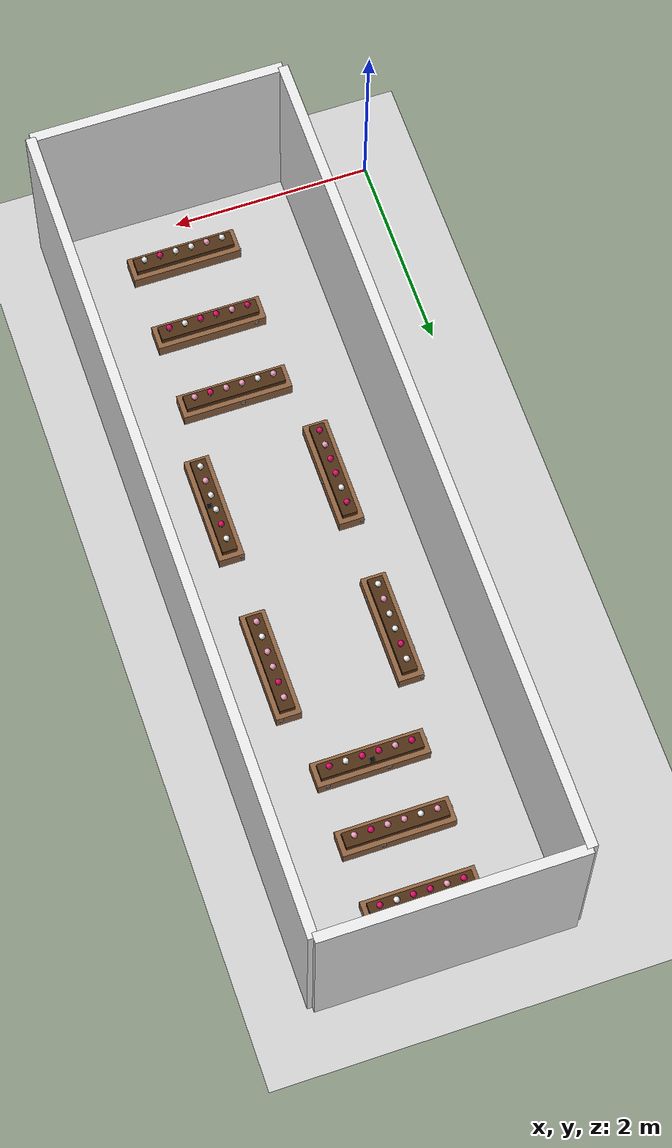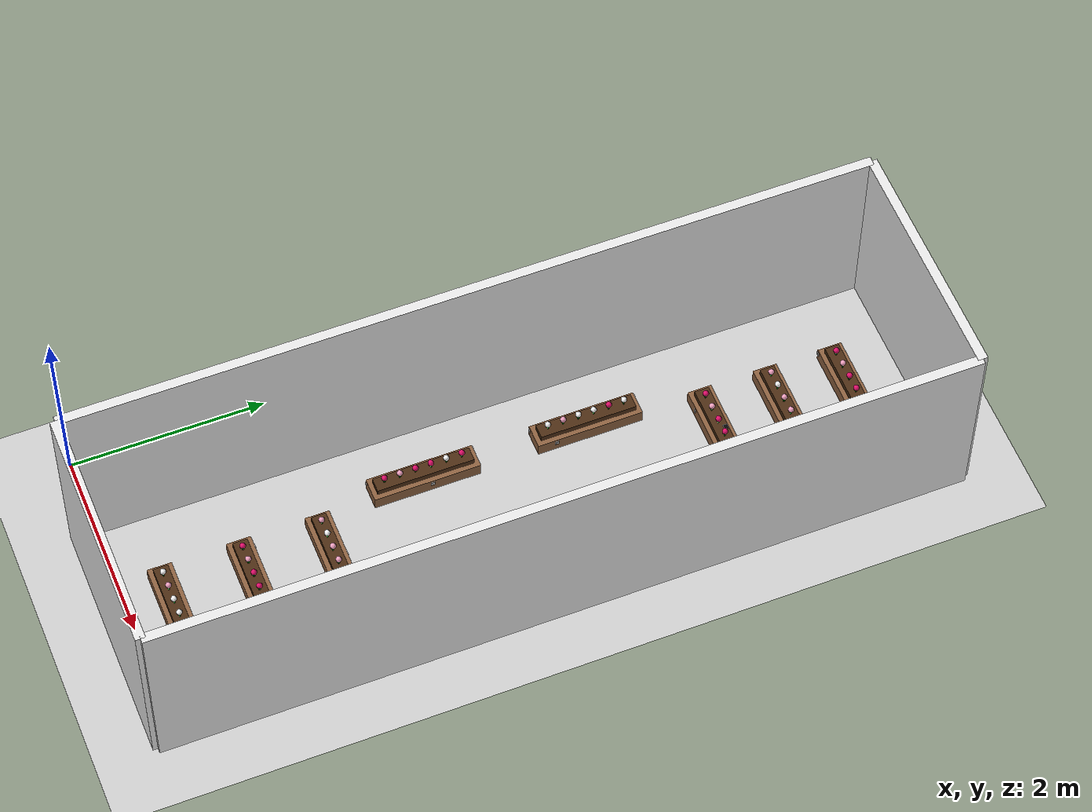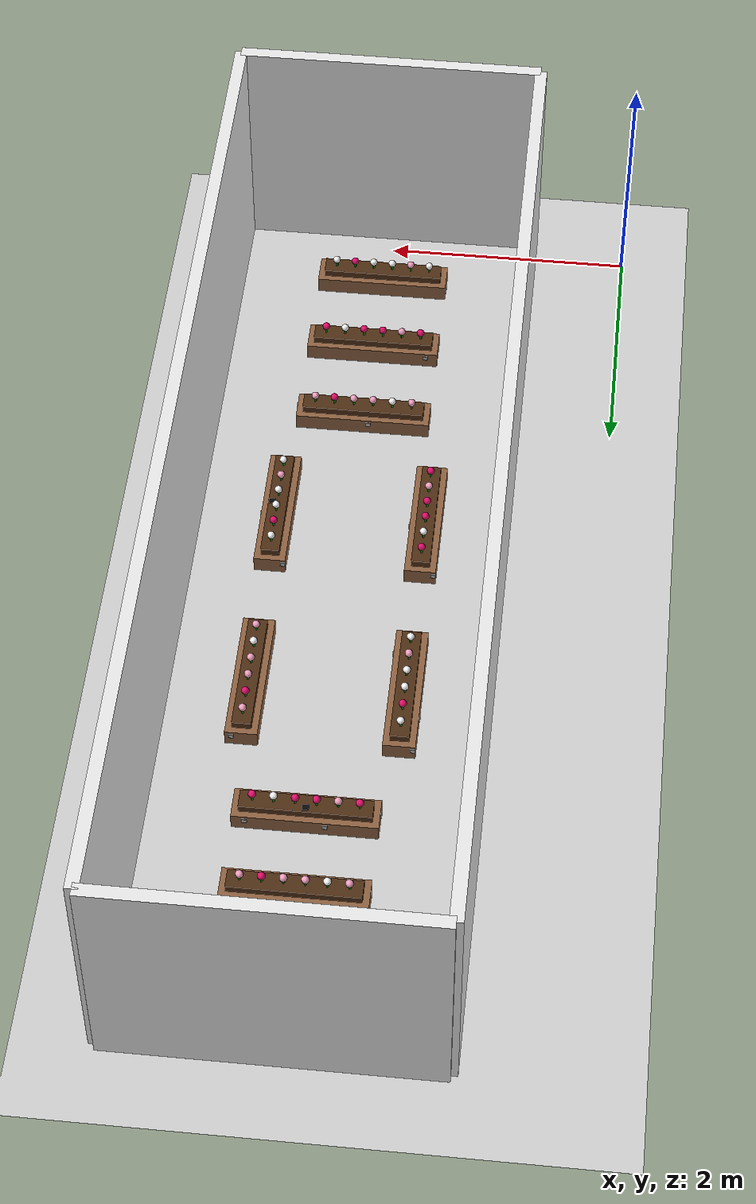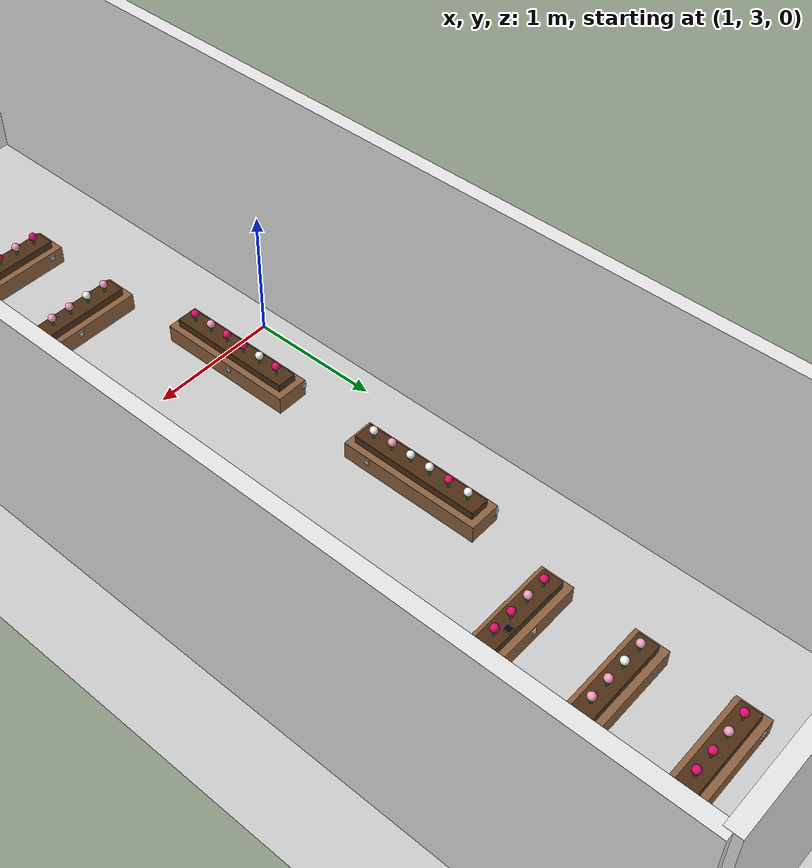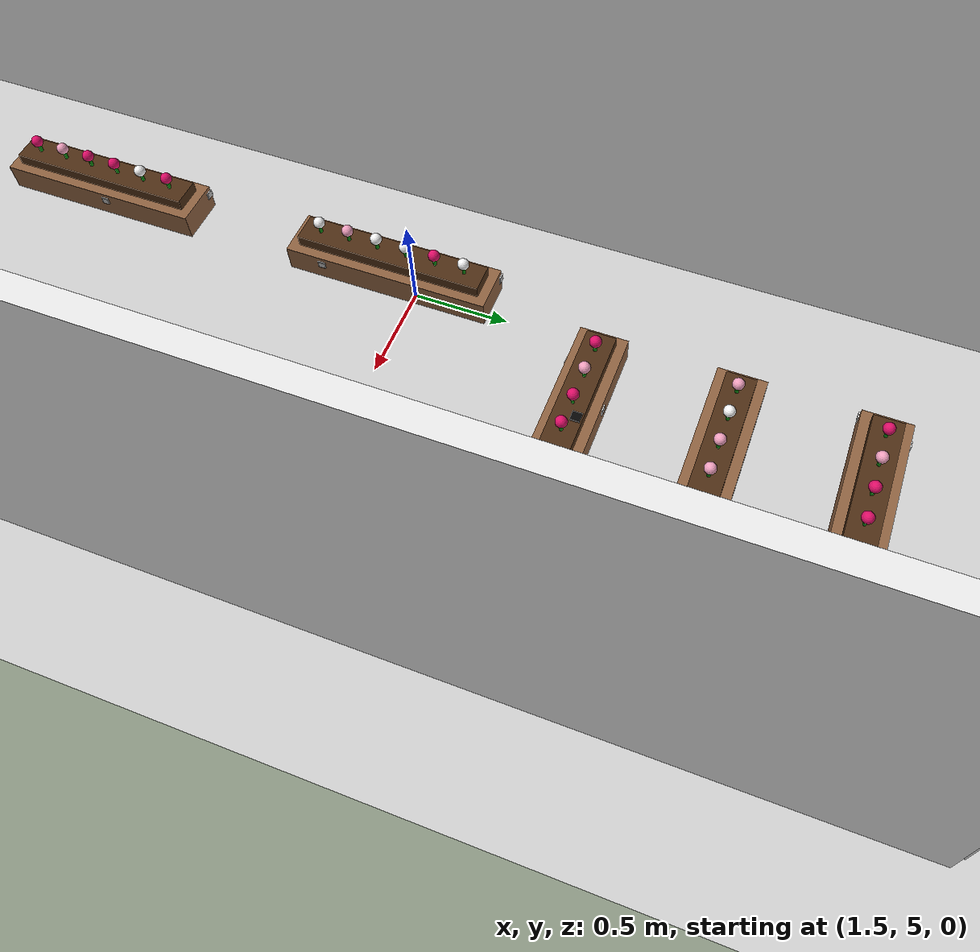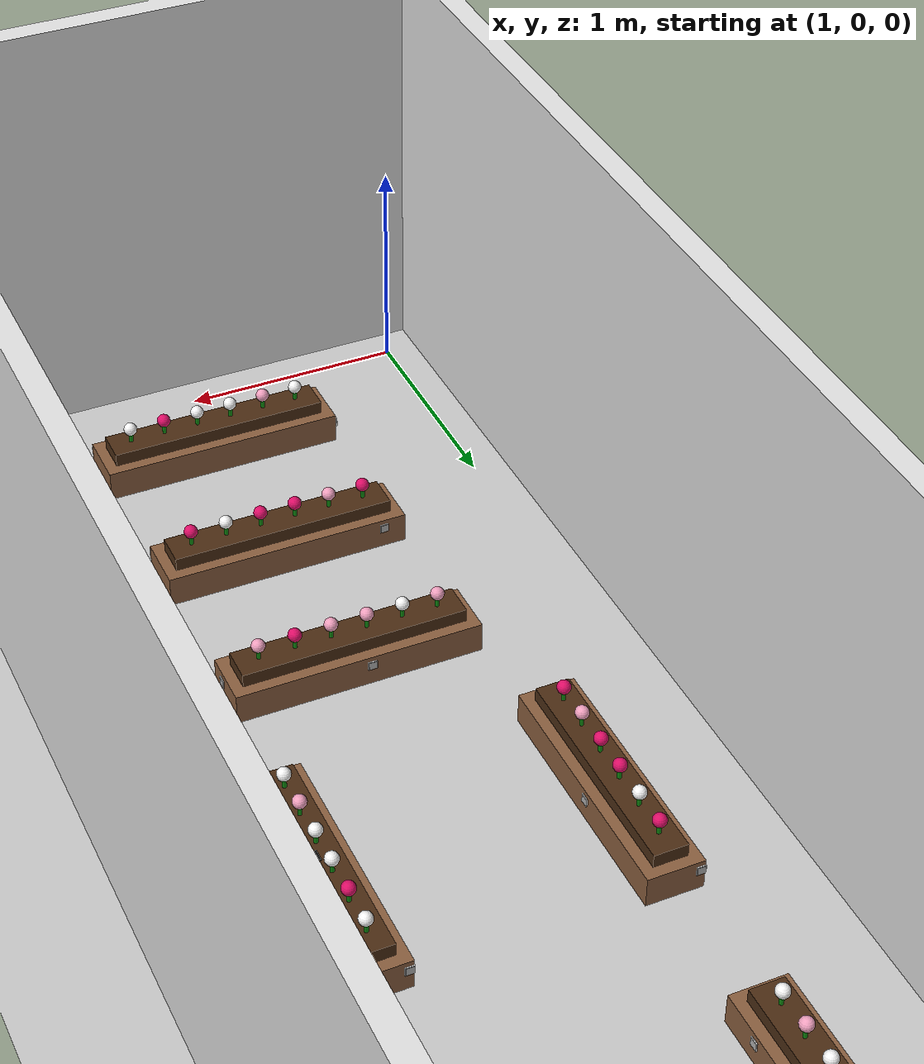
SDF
<?xml version="1.0" ?>
<sdf version="1.6">
  <world name="greenhouse">
    <include><uri>model://sun</uri></include>
    <include><uri>model://ground_plane</uri></include>

    <physics type="ode">
      <max_step_size>0.001</max_step_size>
      <real_time_factor>1.0</real_time_factor>
      <real_time_update_rate>1000</real_time_update_rate>
    </physics>

    <model name="wall_south">
      <static>true</static>
      <pose>2.0500 -0.2000 1.0000 0 0 0</pose>
      <link name="link">
        <collision name="collision">
          <geometry><box><size>2.5000 0.1000 2.0000</size></box></geometry>
        </collision>
        <visual name="visual">
          <geometry><box><size>2.5000 0.1000 2.0000</size></box></geometry>
          <material>
            <ambient>0.85 0.85 0.85 1</ambient>
            <diffuse>0.90 0.90 0.90 1</diffuse>
          </material>
        </visual>
      </link>
    </model>
    <model name="wall_north">
      <static>true</static>
      <pose>2.0500 8.0500 1.0000 0 0 0</pose>
      <link name="link">
        <collision name="collision">
          <geometry><box><size>2.5000 0.1000 2.0000</size></box></geometry>
        </collision>
        <visual name="visual">
          <geometry><box><size>2.5000 0.1000 2.0000</size></box></geometry>
          <material>
            <ambient>0.85 0.85 0.85 1</ambient>
            <diffuse>0.90 0.90 0.90 1</diffuse>
          </material>
        </visual>
      </link>
    </model>
    <model name="wall_west">
      <static>true</static>
      <pose>0.8000 3.9250 1.0000 0 0 0</pose>
      <link name="link">
        <collision name="collision">
          <geometry><box><size>0.1000 8.2500 2.0000</size></box></geometry>
        </collision>
        <visual name="visual">
          <geometry><box><size>0.1000 8.2500 2.0000</size></box></geometry>
          <material>
            <ambient>0.85 0.85 0.85 1</ambient>
            <diffuse>0.90 0.90 0.90 1</diffuse>
          </material>
        </visual>
      </link>
    </model>
    <model name="wall_east">
      <static>true</static>
      <pose>3.3000 3.9250 1.0000 0 0 0</pose>
      <link name="link">
        <collision name="collision">
          <geometry><box><size>0.1000 8.2500 2.0000</size></box></geometry>
        </collision>
        <visual name="visual">
          <geometry><box><size>0.1000 8.2500 2.0000</size></box></geometry>
          <material>
            <ambient>0.85 0.85 0.85 1</ambient>
            <diffuse>0.90 0.90 0.90 1</diffuse>
          </material>
        </visual>
      </link>
    </model>
    <model name="table1">
      <static>true</static>
      <pose>2.0500 7.4250 0.0700 0 0 0</pose>
      <link name="link">
        <collision name="collision">
          <geometry><box><size>1.1000 0.2500 0.1400</size></box></geometry>
        </collision>
        <visual name="visual">
          <geometry><box><size>1.1000 0.2500 0.1400</size></box></geometry>
          <material>
            <ambient>0.45 0.30 0.20 1</ambient>
            <diffuse>0.55 0.38 0.25 1</diffuse>
          </material>
        </visual>
      </link>
    </model>
    <model name="table10">
      <static>true</static>
      <pose>2.0500 0.4250 0.0700 0 0 0</pose>
      <link name="link">
        <collision name="collision">
          <geometry><box><size>1.1000 0.2500 0.1400</size></box></geometry>
        </collision>
        <visual name="visual">
          <geometry><box><size>1.1000 0.2500 0.1400</size></box></geometry>
          <material>
            <ambient>0.45 0.30 0.20 1</ambient>
            <diffuse>0.55 0.38 0.25 1</diffuse>
          </material>
        </visual>
      </link>
    </model>
    <model name="table2">
      <static>true</static>
      <pose>2.0500 6.7250 0.0700 0 0 0</pose>
      <link name="link">
        <collision name="collision">
          <geometry><box><size>1.1000 0.2500 0.1400</size></box></geometry>
        </collision>
        <visual name="visual">
          <geometry><box><size>1.1000 0.2500 0.1400</size></box></geometry>
          <material>
            <ambient>0.45 0.30 0.20 1</ambient>
            <diffuse>0.55 0.38 0.25 1</diffuse>
          </material>
        </visual>
      </link>
    </model>
    <model name="table3">
      <static>true</static>
      <pose>2.0500 6.0250 0.0700 0 0 0</pose>
      <link name="link">
        <collision name="collision">
          <geometry><box><size>1.1000 0.2500 0.1400</size></box></geometry>
        </collision>
        <visual name="visual">
          <geometry><box><size>1.1000 0.2500 0.1400</size></box></geometry>
          <material>
            <ambient>0.45 0.30 0.20 1</ambient>
            <diffuse>0.55 0.38 0.25 1</diffuse>
          </material>
        </visual>
      </link>
    </model>
    <model name="table4">
      <static>true</static>
      <pose>1.4250 4.8500 0.0700 0 0 0</pose>
      <link name="link">
        <collision name="collision">
          <geometry><box><size>0.2500 1.1000 0.1400</size></box></geometry>
        </collision>
        <visual name="visual">
          <geometry><box><size>0.2500 1.1000 0.1400</size></box></geometry>
          <material>
            <ambient>0.45 0.30 0.20 1</ambient>
            <diffuse>0.55 0.38 0.25 1</diffuse>
          </material>
        </visual>
      </link>
    </model>
    <model name="table5">
      <static>true</static>
      <pose>2.6250 4.8500 0.0700 0 0 0</pose>
      <link name="link">
        <collision name="collision">
          <geometry><box><size>0.2500 1.1000 0.1400</size></box></geometry>
        </collision>
        <visual name="visual">
          <geometry><box><size>0.2500 1.1000 0.1400</size></box></geometry>
          <material>
            <ambient>0.45 0.30 0.20 1</ambient>
            <diffuse>0.55 0.38 0.25 1</diffuse>
          </material>
        </visual>
      </link>
    </model>
    <model name="table6">
      <static>true</static>
      <pose>1.4250 3.1500 0.0700 0 0 0</pose>
      <link name="link">
        <collision name="collision">
          <geometry><box><size>0.2500 1.1000 0.1400</size></box></geometry>
        </collision>
        <visual name="visual">
          <geometry><box><size>0.2500 1.1000 0.1400</size></box></geometry>
          <material>
            <ambient>0.45 0.30 0.20 1</ambient>
            <diffuse>0.55 0.38 0.25 1</diffuse>
          </material>
        </visual>
      </link>
    </model>
    <model name="table7">
      <static>true</static>
      <pose>2.6250 3.1500 0.0700 0 0 0</pose>
      <link name="link">
        <collision name="collision">
          <geometry><box><size>0.2500 1.1000 0.1400</size></box></geometry>
        </collision>
        <visual name="visual">
          <geometry><box><size>0.2500 1.1000 0.1400</size></box></geometry>
          <material>
            <ambient>0.45 0.30 0.20 1</ambient>
            <diffuse>0.55 0.38 0.25 1</diffuse>
          </material>
        </visual>
      </link>
    </model>
    <model name="table8">
      <static>true</static>
      <pose>2.0500 2.0250 0.0700 0 0 0</pose>
      <link name="link">
        <collision name="collision">
          <geometry><box><size>1.1000 0.2500 0.1400</size></box></geometry>
        </collision>
        <visual name="visual">
          <geometry><box><size>1.1000 0.2500 0.1400</size></box></geometry>
          <material>
            <ambient>0.45 0.30 0.20 1</ambient>
            <diffuse>0.55 0.38 0.25 1</diffuse>
          </material>
        </visual>
      </link>
    </model>
    <model name="table9">
      <static>true</static>
      <pose>2.0500 1.2250 0.0700 0 0 0</pose>
      <link name="link">
        <collision name="collision">
          <geometry><box><size>1.1000 0.2500 0.1400</size></box></geometry>
        </collision>
        <visual name="visual">
          <geometry><box><size>1.1000 0.2500 0.1400</size></box></geometry>
          <material>
            <ambient>0.45 0.30 0.20 1</ambient>
            <diffuse>0.55 0.38 0.25 1</diffuse>
          </material>
        </visual>
      </link>
    </model>
    <model name="trough_table_0">
      <static>true</static>
      <pose>2.0500 7.4250 0.1700 0 0 0</pose>
      <link name="link">
        <visual name="visual">
          <geometry><box><size>1.0000 0.1500 0.0600</size></box></geometry>
          <material>
            <ambient>0.20 0.12 0.05 1</ambient>
            <diffuse>0.30 0.18 0.08 1</diffuse>
          </material>
        </visual>
      </link>
    </model>
    <model name="flower_0_red">
      <static>true</static>
      <pose>1.6500 7.4250 0 0 0 0</pose>
      <link name="link">
        <visual name="stem">
          <pose>0 0 0.2250 0 0 0</pose>
          <geometry><cylinder><radius>0.009</radius><length>0.0500</length></cylinder></geometry>
          <material><ambient>0.05 0.40 0.05 1</ambient><diffuse>0.05 0.52 0.05 1</diffuse></material>
        </visual>
        <visual name="blossom">
          <pose>0 0 0.2665 0 0 0</pose>
          <geometry><sphere><radius>0.0300</radius></sphere></geometry>
          <material>
            <ambient>0.32 0.02 0.15 1</ambient>
            <diffuse>0.86 0.05 0.40 1</diffuse>
            <emissive>0.40 0.00 0.18 1</emissive>
          </material>
        </visual>
      </link>
    </model>
    <model name="flower_1_pink">
      <static>true</static>
      <pose>1.8100 7.4250 0 0 0 0</pose>
      <link name="link">
        <visual name="stem">
          <pose>0 0 0.2250 0 0 0</pose>
          <geometry><cylinder><radius>0.009</radius><length>0.0500</length></cylinder></geometry>
          <material><ambient>0.05 0.40 0.05 1</ambient><diffuse>0.05 0.52 0.05 1</diffuse></material>
        </visual>
        <visual name="blossom">
          <pose>0 0 0.2665 0 0 0</pose>
          <geometry><sphere><radius>0.0300</radius></sphere></geometry>
          <material>
            <ambient>0.40 0.26 0.31 1</ambient>
            <diffuse>0.93 0.62 0.74 1</diffuse>
            <emissive>0.18 0.06 0.11 1</emissive>
          </material>
        </visual>
      </link>
    </model>
    <model name="flower_2_red">
      <static>true</static>
      <pose>1.9700 7.4250 0 0 0 0</pose>
      <link name="link">
        <visual name="stem">
          <pose>0 0 0.2250 0 0 0</pose>
          <geometry><cylinder><radius>0.009</radius><length>0.0500</length></cylinder></geometry>
          <material><ambient>0.05 0.40 0.05 1</ambient><diffuse>0.05 0.52 0.05 1</diffuse></material>
        </visual>
        <visual name="blossom">
          <pose>0 0 0.2665 0 0 0</pose>
          <geometry><sphere><radius>0.0300</radius></sphere></geometry>
          <material>
            <ambient>0.32 0.02 0.15 1</ambient>
            <diffuse>0.86 0.05 0.40 1</diffuse>
            <emissive>0.40 0.00 0.18 1</emissive>
          </material>
        </visual>
      </link>
    </model>
    <model name="flower_3_red">
      <static>true</static>
      <pose>2.1300 7.4250 0 0 0 0</pose>
      <link name="link">
        <visual name="stem">
          <pose>0 0 0.2250 0 0 0</pose>
          <geometry><cylinder><radius>0.009</radius><length>0.0500</length></cylinder></geometry>
          <material><ambient>0.05 0.40 0.05 1</ambient><diffuse>0.05 0.52 0.05 1</diffuse></material>
        </visual>
        <visual name="blossom">
          <pose>0 0 0.2665 0 0 0</pose>
          <geometry><sphere><radius>0.0300</radius></sphere></geometry>
          <material>
            <ambient>0.32 0.02 0.15 1</ambient>
            <diffuse>0.86 0.05 0.40 1</diffuse>
            <emissive>0.40 0.00 0.18 1</emissive>
          </material>
        </visual>
      </link>
    </model>
    <model name="flower_4_white">
      <static>true</static>
      <pose>2.2900 7.4250 0 0 0 0</pose>
      <link name="link">
        <visual name="stem">
          <pose>0 0 0.2250 0 0 0</pose>
          <geometry><cylinder><radius>0.009</radius><length>0.0500</length></cylinder></geometry>
          <material><ambient>0.05 0.40 0.05 1</ambient><diffuse>0.05 0.52 0.05 1</diffuse></material>
        </visual>
        <visual name="blossom">
          <pose>0 0 0.2665 0 0 0</pose>
          <geometry><sphere><radius>0.0300</radius></sphere></geometry>
          <material>
            <ambient>0.42 0.42 0.42 1</ambient>
            <diffuse>0.95 0.95 0.95 1</diffuse>
            <emissive>0.40 0.40 0.40 1</emissive>
          </material>
        </visual>
      </link>
    </model>
    <model name="flower_5_red">
      <static>true</static>
      <pose>2.4500 7.4250 0 0 0 0</pose>
      <link name="link">
        <visual name="stem">
          <pose>0 0 0.2250 0 0 0</pose>
          <geometry><cylinder><radius>0.009</radius><length>0.0500</length></cylinder></geometry>
          <material><ambient>0.05 0.40 0.05 1</ambient><diffuse>0.05 0.52 0.05 1</diffuse></material>
        </visual>
        <visual name="blossom">
          <pose>0 0 0.2665 0 0 0</pose>
          <geometry><sphere><radius>0.0300</radius></sphere></geometry>
          <material>
            <ambient>0.32 0.02 0.15 1</ambient>
            <diffuse>0.86 0.05 0.40 1</diffuse>
            <emissive>0.40 0.00 0.18 1</emissive>
          </material>
        </visual>
      </link>
    </model>
    <model name="trough_table_1">
      <static>true</static>
      <pose>2.0500 0.4250 0.1700 0 0 0</pose>
      <link name="link">
        <visual name="visual">
          <geometry><box><size>1.0000 0.1500 0.0600</size></box></geometry>
          <material>
            <ambient>0.20 0.12 0.05 1</ambient>
            <diffuse>0.30 0.18 0.08 1</diffuse>
          </material>
        </visual>
      </link>
    </model>
    <model name="flower_6_white">
      <static>true</static>
      <pose>1.6500 0.4250 0 0 0 0</pose>
      <link name="link">
        <visual name="stem">
          <pose>0 0 0.2250 0 0 0</pose>
          <geometry><cylinder><radius>0.009</radius><length>0.0500</length></cylinder></geometry>
          <material><ambient>0.05 0.40 0.05 1</ambient><diffuse>0.05 0.52 0.05 1</diffuse></material>
        </visual>
        <visual name="blossom">
          <pose>0 0 0.2665 0 0 0</pose>
          <geometry><sphere><radius>0.0300</radius></sphere></geometry>
          <material>
            <ambient>0.42 0.42 0.42 1</ambient>
            <diffuse>0.95 0.95 0.95 1</diffuse>
            <emissive>0.40 0.40 0.40 1</emissive>
          </material>
        </visual>
      </link>
    </model>
    <model name="flower_7_pink">
      <static>true</static>
      <pose>1.8100 0.4250 0 0 0 0</pose>
      <link name="link">
        <visual name="stem">
          <pose>0 0 0.2250 0 0 0</pose>
          <geometry><cylinder><radius>0.009</radius><length>0.0500</length></cylinder></geometry>
          <material><ambient>0.05 0.40 0.05 1</ambient><diffuse>0.05 0.52 0.05 1</diffuse></material>
        </visual>
        <visual name="blossom">
          <pose>0 0 0.2665 0 0 0</pose>
          <geometry><sphere><radius>0.0300</radius></sphere></geometry>
          <material>
            <ambient>0.40 0.26 0.31 1</ambient>
            <diffuse>0.93 0.62 0.74 1</diffuse>
            <emissive>0.18 0.06 0.11 1</emissive>
          </material>
        </visual>
      </link>
    </model>
    <model name="flower_8_white">
      <static>true</static>
      <pose>1.9700 0.4250 0 0 0 0</pose>
      <link name="link">
        <visual name="stem">
          <pose>0 0 0.2250 0 0 0</pose>
          <geometry><cylinder><radius>0.009</radius><length>0.0500</length></cylinder></geometry>
          <material><ambient>0.05 0.40 0.05 1</ambient><diffuse>0.05 0.52 0.05 1</diffuse></material>
        </visual>
        <visual name="blossom">
          <pose>0 0 0.2665 0 0 0</pose>
          <geometry><sphere><radius>0.0300</radius></sphere></geometry>
          <material>
            <ambient>0.42 0.42 0.42 1</ambient>
            <diffuse>0.95 0.95 0.95 1</diffuse>
            <emissive>0.40 0.40 0.40 1</emissive>
          </material>
        </visual>
      </link>
    </model>
    <model name="flower_9_white">
      <static>true</static>
      <pose>2.1300 0.4250 0 0 0 0</pose>
      <link name="link">
        <visual name="stem">
          <pose>0 0 0.2250 0 0 0</pose>
          <geometry><cylinder><radius>0.009</radius><length>0.0500</length></cylinder></geometry>
          <material><ambient>0.05 0.40 0.05 1</ambient><diffuse>0.05 0.52 0.05 1</diffuse></material>
        </visual>
        <visual name="blossom">
          <pose>0 0 0.2665 0 0 0</pose>
          <geometry><sphere><radius>0.0300</radius></sphere></geometry>
          <material>
            <ambient>0.42 0.42 0.42 1</ambient>
            <diffuse>0.95 0.95 0.95 1</diffuse>
            <emissive>0.40 0.40 0.40 1</emissive>
          </material>
        </visual>
      </link>
    </model>
    <model name="flower_10_red">
      <static>true</static>
      <pose>2.2900 0.4250 0 0 0 0</pose>
      <link name="link">
        <visual name="stem">
          <pose>0 0 0.2250 0 0 0</pose>
          <geometry><cylinder><radius>0.009</radius><length>0.0500</length></cylinder></geometry>
          <material><ambient>0.05 0.40 0.05 1</ambient><diffuse>0.05 0.52 0.05 1</diffuse></material>
        </visual>
        <visual name="blossom">
          <pose>0 0 0.2665 0 0 0</pose>
          <geometry><sphere><radius>0.0300</radius></sphere></geometry>
          <material>
            <ambient>0.32 0.02 0.15 1</ambient>
            <diffuse>0.86 0.05 0.40 1</diffuse>
            <emissive>0.40 0.00 0.18 1</emissive>
          </material>
        </visual>
      </link>
    </model>
    <model name="flower_11_white">
      <static>true</static>
      <pose>2.4500 0.4250 0 0 0 0</pose>
      <link name="link">
        <visual name="stem">
          <pose>0 0 0.2250 0 0 0</pose>
          <geometry><cylinder><radius>0.009</radius><length>0.0500</length></cylinder></geometry>
          <material><ambient>0.05 0.40 0.05 1</ambient><diffuse>0.05 0.52 0.05 1</diffuse></material>
        </visual>
        <visual name="blossom">
          <pose>0 0 0.2665 0 0 0</pose>
          <geometry><sphere><radius>0.0300</radius></sphere></geometry>
          <material>
            <ambient>0.42 0.42 0.42 1</ambient>
            <diffuse>0.95 0.95 0.95 1</diffuse>
            <emissive>0.40 0.40 0.40 1</emissive>
          </material>
        </visual>
      </link>
    </model>
    <model name="trough_table_2">
      <static>true</static>
      <pose>2.0500 6.7250 0.1700 0 0 0</pose>
      <link name="link">
        <visual name="visual">
          <geometry><box><size>1.0000 0.1500 0.0600</size></box></geometry>
          <material>
            <ambient>0.20 0.12 0.05 1</ambient>
            <diffuse>0.30 0.18 0.08 1</diffuse>
          </material>
        </visual>
      </link>
    </model>
    <model name="flower_12_pink">
      <static>true</static>
      <pose>1.6500 6.7250 0 0 0 0</pose>
      <link name="link">
        <visual name="stem">
          <pose>0 0 0.2250 0 0 0</pose>
          <geometry><cylinder><radius>0.009</radius><length>0.0500</length></cylinder></geometry>
          <material><ambient>0.05 0.40 0.05 1</ambient><diffuse>0.05 0.52 0.05 1</diffuse></material>
        </visual>
        <visual name="blossom">
          <pose>0 0 0.2665 0 0 0</pose>
          <geometry><sphere><radius>0.0300</radius></sphere></geometry>
          <material>
            <ambient>0.40 0.26 0.31 1</ambient>
            <diffuse>0.93 0.62 0.74 1</diffuse>
            <emissive>0.18 0.06 0.11 1</emissive>
          </material>
        </visual>
      </link>
    </model>
    <model name="flower_13_white">
      <static>true</static>
      <pose>1.8100 6.7250 0 0 0 0</pose>
      <link name="link">
        <visual name="stem">
          <pose>0 0 0.2250 0 0 0</pose>
          <geometry><cylinder><radius>0.009</radius><length>0.0500</length></cylinder></geometry>
          <material><ambient>0.05 0.40 0.05 1</ambient><diffuse>0.05 0.52 0.05 1</diffuse></material>
        </visual>
        <visual name="blossom">
          <pose>0 0 0.2665 0 0 0</pose>
          <geometry><sphere><radius>0.0300</radius></sphere></geometry>
          <material>
            <ambient>0.42 0.42 0.42 1</ambient>
            <diffuse>0.95 0.95 0.95 1</diffuse>
            <emissive>0.40 0.40 0.40 1</emissive>
          </material>
        </visual>
      </link>
    </model>
    <model name="flower_14_pink">
      <static>true</static>
      <pose>1.9700 6.7250 0 0 0 0</pose>
      <link name="link">
        <visual name="stem">
          <pose>0 0 0.2250 0 0 0</pose>
          <geometry><cylinder><radius>0.009</radius><length>0.0500</length></cylinder></geometry>
          <material><ambient>0.05 0.40 0.05 1</ambient><diffuse>0.05 0.52 0.05 1</diffuse></material>
        </visual>
        <visual name="blossom">
          <pose>0 0 0.2665 0 0 0</pose>
          <geometry><sphere><radius>0.0300</radius></sphere></geometry>
          <material>
            <ambient>0.40 0.26 0.31 1</ambient>
            <diffuse>0.93 0.62 0.74 1</diffuse>
            <emissive>0.18 0.06 0.11 1</emissive>
          </material>
        </visual>
      </link>
    </model>
    <model name="flower_15_pink">
      <static>true</static>
      <pose>2.1300 6.7250 0 0 0 0</pose>
      <link name="link">
        <visual name="stem">
          <pose>0 0 0.2250 0 0 0</pose>
          <geometry><cylinder><radius>0.009</radius><length>0.0500</length></cylinder></geometry>
          <material><ambient>0.05 0.40 0.05 1</ambient><diffuse>0.05 0.52 0.05 1</diffuse></material>
        </visual>
        <visual name="blossom">
          <pose>0 0 0.2665 0 0 0</pose>
          <geometry><sphere><radius>0.0300</radius></sphere></geometry>
          <material>
            <ambient>0.40 0.26 0.31 1</ambient>
            <diffuse>0.93 0.62 0.74 1</diffuse>
            <emissive>0.18 0.06 0.11 1</emissive>
          </material>
        </visual>
      </link>
    </model>
    <model name="flower_16_red">
      <static>true</static>
      <pose>2.2900 6.7250 0 0 0 0</pose>
      <link name="link">
        <visual name="stem">
          <pose>0 0 0.2250 0 0 0</pose>
          <geometry><cylinder><radius>0.009</radius><length>0.0500</length></cylinder></geometry>
          <material><ambient>0.05 0.40 0.05 1</ambient><diffuse>0.05 0.52 0.05 1</diffuse></material>
        </visual>
        <visual name="blossom">
          <pose>0 0 0.2665 0 0 0</pose>
          <geometry><sphere><radius>0.0300</radius></sphere></geometry>
          <material>
            <ambient>0.32 0.02 0.15 1</ambient>
            <diffuse>0.86 0.05 0.40 1</diffuse>
            <emissive>0.40 0.00 0.18 1</emissive>
          </material>
        </visual>
      </link>
    </model>
    <model name="flower_17_pink">
      <static>true</static>
      <pose>2.4500 6.7250 0 0 0 0</pose>
      <link name="link">
        <visual name="stem">
          <pose>0 0 0.2250 0 0 0</pose>
          <geometry><cylinder><radius>0.009</radius><length>0.0500</length></cylinder></geometry>
          <material><ambient>0.05 0.40 0.05 1</ambient><diffuse>0.05 0.52 0.05 1</diffuse></material>
        </visual>
        <visual name="blossom">
          <pose>0 0 0.2665 0 0 0</pose>
          <geometry><sphere><radius>0.0300</radius></sphere></geometry>
          <material>
            <ambient>0.40 0.26 0.31 1</ambient>
            <diffuse>0.93 0.62 0.74 1</diffuse>
            <emissive>0.18 0.06 0.11 1</emissive>
          </material>
        </visual>
      </link>
    </model>
    <model name="trough_table_3">
      <static>true</static>
      <pose>2.0500 6.0250 0.1700 0 0 0</pose>
      <link name="link">
        <visual name="visual">
          <geometry><box><size>1.0000 0.1500 0.0600</size></box></geometry>
          <material>
            <ambient>0.20 0.12 0.05 1</ambient>
            <diffuse>0.30 0.18 0.08 1</diffuse>
          </material>
        </visual>
      </link>
    </model>
    <model name="flower_18_red">
      <static>true</static>
      <pose>1.6500 6.0250 0 0 0 0</pose>
      <link name="link">
        <visual name="stem">
          <pose>0 0 0.2250 0 0 0</pose>
          <geometry><cylinder><radius>0.009</radius><length>0.0500</length></cylinder></geometry>
          <material><ambient>0.05 0.40 0.05 1</ambient><diffuse>0.05 0.52 0.05 1</diffuse></material>
        </visual>
        <visual name="blossom">
          <pose>0 0 0.2665 0 0 0</pose>
          <geometry><sphere><radius>0.0300</radius></sphere></geometry>
          <material>
            <ambient>0.32 0.02 0.15 1</ambient>
            <diffuse>0.86 0.05 0.40 1</diffuse>
            <emissive>0.40 0.00 0.18 1</emissive>
          </material>
        </visual>
      </link>
    </model>
    <model name="flower_19_pink">
      <static>true</static>
      <pose>1.8100 6.0250 0 0 0 0</pose>
      <link name="link">
        <visual name="stem">
          <pose>0 0 0.2250 0 0 0</pose>
          <geometry><cylinder><radius>0.009</radius><length>0.0500</length></cylinder></geometry>
          <material><ambient>0.05 0.40 0.05 1</ambient><diffuse>0.05 0.52 0.05 1</diffuse></material>
        </visual>
        <visual name="blossom">
          <pose>0 0 0.2665 0 0 0</pose>
          <geometry><sphere><radius>0.0300</radius></sphere></geometry>
          <material>
            <ambient>0.40 0.26 0.31 1</ambient>
            <diffuse>0.93 0.62 0.74 1</diffuse>
            <emissive>0.18 0.06 0.11 1</emissive>
          </material>
        </visual>
      </link>
    </model>
    <model name="flower_20_red">
      <static>true</static>
      <pose>1.9700 6.0250 0 0 0 0</pose>
      <link name="link">
        <visual name="stem">
          <pose>0 0 0.2250 0 0 0</pose>
          <geometry><cylinder><radius>0.009</radius><length>0.0500</length></cylinder></geometry>
          <material><ambient>0.05 0.40 0.05 1</ambient><diffuse>0.05 0.52 0.05 1</diffuse></material>
        </visual>
        <visual name="blossom">
          <pose>0 0 0.2665 0 0 0</pose>
          <geometry><sphere><radius>0.0300</radius></sphere></geometry>
          <material>
            <ambient>0.32 0.02 0.15 1</ambient>
            <diffuse>0.86 0.05 0.40 1</diffuse>
            <emissive>0.40 0.00 0.18 1</emissive>
          </material>
        </visual>
      </link>
    </model>
    <model name="flower_21_red">
      <static>true</static>
      <pose>2.1300 6.0250 0 0 0 0</pose>
      <link name="link">
        <visual name="stem">
          <pose>0 0 0.2250 0 0 0</pose>
          <geometry><cylinder><radius>0.009</radius><length>0.0500</length></cylinder></geometry>
          <material><ambient>0.05 0.40 0.05 1</ambient><diffuse>0.05 0.52 0.05 1</diffuse></material>
        </visual>
        <visual name="blossom">
          <pose>0 0 0.2665 0 0 0</pose>
          <geometry><sphere><radius>0.0300</radius></sphere></geometry>
          <material>
            <ambient>0.32 0.02 0.15 1</ambient>
            <diffuse>0.86 0.05 0.40 1</diffuse>
            <emissive>0.40 0.00 0.18 1</emissive>
          </material>
        </visual>
      </link>
    </model>
    <model name="flower_22_white">
      <static>true</static>
      <pose>2.2900 6.0250 0 0 0 0</pose>
      <link name="link">
        <visual name="stem">
          <pose>0 0 0.2250 0 0 0</pose>
          <geometry><cylinder><radius>0.009</radius><length>0.0500</length></cylinder></geometry>
          <material><ambient>0.05 0.40 0.05 1</ambient><diffuse>0.05 0.52 0.05 1</diffuse></material>
        </visual>
        <visual name="blossom">
          <pose>0 0 0.2665 0 0 0</pose>
          <geometry><sphere><radius>0.0300</radius></sphere></geometry>
          <material>
            <ambient>0.42 0.42 0.42 1</ambient>
            <diffuse>0.95 0.95 0.95 1</diffuse>
            <emissive>0.40 0.40 0.40 1</emissive>
          </material>
        </visual>
      </link>
    </model>
    <model name="flower_23_red">
      <static>true</static>
      <pose>2.4500 6.0250 0 0 0 0</pose>
      <link name="link">
        <visual name="stem">
          <pose>0 0 0.2250 0 0 0</pose>
          <geometry><cylinder><radius>0.009</radius><length>0.0500</length></cylinder></geometry>
          <material><ambient>0.05 0.40 0.05 1</ambient><diffuse>0.05 0.52 0.05 1</diffuse></material>
        </visual>
        <visual name="blossom">
          <pose>0 0 0.2665 0 0 0</pose>
          <geometry><sphere><radius>0.0300</radius></sphere></geometry>
          <material>
            <ambient>0.32 0.02 0.15 1</ambient>
            <diffuse>0.86 0.05 0.40 1</diffuse>
            <emissive>0.40 0.00 0.18 1</emissive>
          </material>
        </visual>
      </link>
    </model>
    <model name="bug_24">
      <static>true</static>
      <pose>2.0500 6.0700 0.2150 0 0 0</pose>
      <link name="link">
        <visual name="visual">
          <geometry><box><size>0.0500 0.0500 0.008</size></box></geometry>
          <material>
            <ambient>0.02 0.02 0.02 1</ambient>
            <diffuse>0.02 0.02 0.02 1</diffuse>
          </material>
        </visual>
      </link>
    </model>
    <model name="trough_table_4">
      <static>true</static>
      <pose>1.4250 4.8500 0.1700 0 0 0</pose>
      <link name="link">
        <visual name="visual">
          <geometry><box><size>0.1500 1.0000 0.0600</size></box></geometry>
          <material>
            <ambient>0.20 0.12 0.05 1</ambient>
            <diffuse>0.30 0.18 0.08 1</diffuse>
          </material>
        </visual>
      </link>
    </model>
    <model name="flower_25_white">
      <static>true</static>
      <pose>1.4250 4.4500 0 0 0 0</pose>
      <link name="link">
        <visual name="stem">
          <pose>0 0 0.2250 0 0 0</pose>
          <geometry><cylinder><radius>0.009</radius><length>0.0500</length></cylinder></geometry>
          <material><ambient>0.05 0.40 0.05 1</ambient><diffuse>0.05 0.52 0.05 1</diffuse></material>
        </visual>
        <visual name="blossom">
          <pose>0 0 0.2665 0 0 0</pose>
          <geometry><sphere><radius>0.0300</radius></sphere></geometry>
          <material>
            <ambient>0.42 0.42 0.42 1</ambient>
            <diffuse>0.95 0.95 0.95 1</diffuse>
            <emissive>0.40 0.40 0.40 1</emissive>
          </material>
        </visual>
      </link>
    </model>
    <model name="flower_26_pink">
      <static>true</static>
      <pose>1.4250 4.6100 0 0 0 0</pose>
      <link name="link">
        <visual name="stem">
          <pose>0 0 0.2250 0 0 0</pose>
          <geometry><cylinder><radius>0.009</radius><length>0.0500</length></cylinder></geometry>
          <material><ambient>0.05 0.40 0.05 1</ambient><diffuse>0.05 0.52 0.05 1</diffuse></material>
        </visual>
        <visual name="blossom">
          <pose>0 0 0.2665 0 0 0</pose>
          <geometry><sphere><radius>0.0300</radius></sphere></geometry>
          <material>
            <ambient>0.40 0.26 0.31 1</ambient>
            <diffuse>0.93 0.62 0.74 1</diffuse>
            <emissive>0.18 0.06 0.11 1</emissive>
          </material>
        </visual>
      </link>
    </model>
    <model name="flower_27_white">
      <static>true</static>
      <pose>1.4250 4.7700 0 0 0 0</pose>
      <link name="link">
        <visual name="stem">
          <pose>0 0 0.2250 0 0 0</pose>
          <geometry><cylinder><radius>0.009</radius><length>0.0500</length></cylinder></geometry>
          <material><ambient>0.05 0.40 0.05 1</ambient><diffuse>0.05 0.52 0.05 1</diffuse></material>
        </visual>
        <visual name="blossom">
          <pose>0 0 0.2665 0 0 0</pose>
          <geometry><sphere><radius>0.0300</radius></sphere></geometry>
          <material>
            <ambient>0.42 0.42 0.42 1</ambient>
            <diffuse>0.95 0.95 0.95 1</diffuse>
            <emissive>0.40 0.40 0.40 1</emissive>
          </material>
        </visual>
      </link>
    </model>
    <model name="flower_28_white">
      <static>true</static>
      <pose>1.4250 4.9300 0 0 0 0</pose>
      <link name="link">
        <visual name="stem">
          <pose>0 0 0.2250 0 0 0</pose>
          <geometry><cylinder><radius>0.009</radius><length>0.0500</length></cylinder></geometry>
          <material><ambient>0.05 0.40 0.05 1</ambient><diffuse>0.05 0.52 0.05 1</diffuse></material>
        </visual>
        <visual name="blossom">
          <pose>0 0 0.2665 0 0 0</pose>
          <geometry><sphere><radius>0.0300</radius></sphere></geometry>
          <material>
            <ambient>0.42 0.42 0.42 1</ambient>
            <diffuse>0.95 0.95 0.95 1</diffuse>
            <emissive>0.40 0.40 0.40 1</emissive>
          </material>
        </visual>
      </link>
    </model>
    <model name="flower_29_red">
      <static>true</static>
      <pose>1.4250 5.0900 0 0 0 0</pose>
      <link name="link">
        <visual name="stem">
          <pose>0 0 0.2250 0 0 0</pose>
          <geometry><cylinder><radius>0.009</radius><length>0.0500</length></cylinder></geometry>
          <material><ambient>0.05 0.40 0.05 1</ambient><diffuse>0.05 0.52 0.05 1</diffuse></material>
        </visual>
        <visual name="blossom">
          <pose>0 0 0.2665 0 0 0</pose>
          <geometry><sphere><radius>0.0300</radius></sphere></geometry>
          <material>
            <ambient>0.32 0.02 0.15 1</ambient>
            <diffuse>0.86 0.05 0.40 1</diffuse>
            <emissive>0.40 0.00 0.18 1</emissive>
          </material>
        </visual>
      </link>
    </model>
    <model name="flower_30_white">
      <static>true</static>
      <pose>1.4250 5.2500 0 0 0 0</pose>
      <link name="link">
        <visual name="stem">
          <pose>0 0 0.2250 0 0 0</pose>
          <geometry><cylinder><radius>0.009</radius><length>0.0500</length></cylinder></geometry>
          <material><ambient>0.05 0.40 0.05 1</ambient><diffuse>0.05 0.52 0.05 1</diffuse></material>
        </visual>
        <visual name="blossom">
          <pose>0 0 0.2665 0 0 0</pose>
          <geometry><sphere><radius>0.0300</radius></sphere></geometry>
          <material>
            <ambient>0.42 0.42 0.42 1</ambient>
            <diffuse>0.95 0.95 0.95 1</diffuse>
            <emissive>0.40 0.40 0.40 1</emissive>
          </material>
        </visual>
      </link>
    </model>
    <model name="trough_table_5">
      <static>true</static>
      <pose>2.6250 4.8500 0.1700 0 0 0</pose>
      <link name="link">
        <visual name="visual">
          <geometry><box><size>0.1500 1.0000 0.0600</size></box></geometry>
          <material>
            <ambient>0.20 0.12 0.05 1</ambient>
            <diffuse>0.30 0.18 0.08 1</diffuse>
          </material>
        </visual>
      </link>
    </model>
    <model name="flower_31_pink">
      <static>true</static>
      <pose>2.6250 4.4500 0 0 0 0</pose>
      <link name="link">
        <visual name="stem">
          <pose>0 0 0.2250 0 0 0</pose>
          <geometry><cylinder><radius>0.009</radius><length>0.0500</length></cylinder></geometry>
          <material><ambient>0.05 0.40 0.05 1</ambient><diffuse>0.05 0.52 0.05 1</diffuse></material>
        </visual>
        <visual name="blossom">
          <pose>0 0 0.2665 0 0 0</pose>
          <geometry><sphere><radius>0.0300</radius></sphere></geometry>
          <material>
            <ambient>0.40 0.26 0.31 1</ambient>
            <diffuse>0.93 0.62 0.74 1</diffuse>
            <emissive>0.18 0.06 0.11 1</emissive>
          </material>
        </visual>
      </link>
    </model>
    <model name="flower_32_white">
      <static>true</static>
      <pose>2.6250 4.6100 0 0 0 0</pose>
      <link name="link">
        <visual name="stem">
          <pose>0 0 0.2250 0 0 0</pose>
          <geometry><cylinder><radius>0.009</radius><length>0.0500</length></cylinder></geometry>
          <material><ambient>0.05 0.40 0.05 1</ambient><diffuse>0.05 0.52 0.05 1</diffuse></material>
        </visual>
        <visual name="blossom">
          <pose>0 0 0.2665 0 0 0</pose>
          <geometry><sphere><radius>0.0300</radius></sphere></geometry>
          <material>
            <ambient>0.42 0.42 0.42 1</ambient>
            <diffuse>0.95 0.95 0.95 1</diffuse>
            <emissive>0.40 0.40 0.40 1</emissive>
          </material>
        </visual>
      </link>
    </model>
    <model name="flower_33_pink">
      <static>true</static>
      <pose>2.6250 4.7700 0 0 0 0</pose>
      <link name="link">
        <visual name="stem">
          <pose>0 0 0.2250 0 0 0</pose>
          <geometry><cylinder><radius>0.009</radius><length>0.0500</length></cylinder></geometry>
          <material><ambient>0.05 0.40 0.05 1</ambient><diffuse>0.05 0.52 0.05 1</diffuse></material>
        </visual>
        <visual name="blossom">
          <pose>0 0 0.2665 0 0 0</pose>
          <geometry><sphere><radius>0.0300</radius></sphere></geometry>
          <material>
            <ambient>0.40 0.26 0.31 1</ambient>
            <diffuse>0.93 0.62 0.74 1</diffuse>
            <emissive>0.18 0.06 0.11 1</emissive>
          </material>
        </visual>
      </link>
    </model>
    <model name="flower_34_pink">
      <static>true</static>
      <pose>2.6250 4.9300 0 0 0 0</pose>
      <link name="link">
        <visual name="stem">
          <pose>0 0 0.2250 0 0 0</pose>
          <geometry><cylinder><radius>0.009</radius><length>0.0500</length></cylinder></geometry>
          <material><ambient>0.05 0.40 0.05 1</ambient><diffuse>0.05 0.52 0.05 1</diffuse></material>
        </visual>
        <visual name="blossom">
          <pose>0 0 0.2665 0 0 0</pose>
          <geometry><sphere><radius>0.0300</radius></sphere></geometry>
          <material>
            <ambient>0.40 0.26 0.31 1</ambient>
            <diffuse>0.93 0.62 0.74 1</diffuse>
            <emissive>0.18 0.06 0.11 1</emissive>
          </material>
        </visual>
      </link>
    </model>
    <model name="flower_35_red">
      <static>true</static>
      <pose>2.6250 5.0900 0 0 0 0</pose>
      <link name="link">
        <visual name="stem">
          <pose>0 0 0.2250 0 0 0</pose>
          <geometry><cylinder><radius>0.009</radius><length>0.0500</length></cylinder></geometry>
          <material><ambient>0.05 0.40 0.05 1</ambient><diffuse>0.05 0.52 0.05 1</diffuse></material>
        </visual>
        <visual name="blossom">
          <pose>0 0 0.2665 0 0 0</pose>
          <geometry><sphere><radius>0.0300</radius></sphere></geometry>
          <material>
            <ambient>0.32 0.02 0.15 1</ambient>
            <diffuse>0.86 0.05 0.40 1</diffuse>
            <emissive>0.40 0.00 0.18 1</emissive>
          </material>
        </visual>
      </link>
    </model>
    <model name="flower_36_pink">
      <static>true</static>
      <pose>2.6250 5.2500 0 0 0 0</pose>
      <link name="link">
        <visual name="stem">
          <pose>0 0 0.2250 0 0 0</pose>
          <geometry><cylinder><radius>0.009</radius><length>0.0500</length></cylinder></geometry>
          <material><ambient>0.05 0.40 0.05 1</ambient><diffuse>0.05 0.52 0.05 1</diffuse></material>
        </visual>
        <visual name="blossom">
          <pose>0 0 0.2665 0 0 0</pose>
          <geometry><sphere><radius>0.0300</radius></sphere></geometry>
          <material>
            <ambient>0.40 0.26 0.31 1</ambient>
            <diffuse>0.93 0.62 0.74 1</diffuse>
            <emissive>0.18 0.06 0.11 1</emissive>
          </material>
        </visual>
      </link>
    </model>
    <model name="trough_table_6">
      <static>true</static>
      <pose>1.4250 3.1500 0.1700 0 0 0</pose>
      <link name="link">
        <visual name="visual">
          <geometry><box><size>0.1500 1.0000 0.0600</size></box></geometry>
          <material>
            <ambient>0.20 0.12 0.05 1</ambient>
            <diffuse>0.30 0.18 0.08 1</diffuse>
          </material>
        </visual>
      </link>
    </model>
    <model name="flower_37_red">
      <static>true</static>
      <pose>1.4250 2.7500 0 0 0 0</pose>
      <link name="link">
        <visual name="stem">
          <pose>0 0 0.2250 0 0 0</pose>
          <geometry><cylinder><radius>0.009</radius><length>0.0500</length></cylinder></geometry>
          <material><ambient>0.05 0.40 0.05 1</ambient><diffuse>0.05 0.52 0.05 1</diffuse></material>
        </visual>
        <visual name="blossom">
          <pose>0 0 0.2665 0 0 0</pose>
          <geometry><sphere><radius>0.0300</radius></sphere></geometry>
          <material>
            <ambient>0.32 0.02 0.15 1</ambient>
            <diffuse>0.86 0.05 0.40 1</diffuse>
            <emissive>0.40 0.00 0.18 1</emissive>
          </material>
        </visual>
      </link>
    </model>
    <model name="flower_38_pink">
      <static>true</static>
      <pose>1.4250 2.9100 0 0 0 0</pose>
      <link name="link">
        <visual name="stem">
          <pose>0 0 0.2250 0 0 0</pose>
          <geometry><cylinder><radius>0.009</radius><length>0.0500</length></cylinder></geometry>
          <material><ambient>0.05 0.40 0.05 1</ambient><diffuse>0.05 0.52 0.05 1</diffuse></material>
        </visual>
        <visual name="blossom">
          <pose>0 0 0.2665 0 0 0</pose>
          <geometry><sphere><radius>0.0300</radius></sphere></geometry>
          <material>
            <ambient>0.40 0.26 0.31 1</ambient>
            <diffuse>0.93 0.62 0.74 1</diffuse>
            <emissive>0.18 0.06 0.11 1</emissive>
          </material>
        </visual>
      </link>
    </model>
    <model name="flower_39_red">
      <static>true</static>
      <pose>1.4250 3.0700 0 0 0 0</pose>
      <link name="link">
        <visual name="stem">
          <pose>0 0 0.2250 0 0 0</pose>
          <geometry><cylinder><radius>0.009</radius><length>0.0500</length></cylinder></geometry>
          <material><ambient>0.05 0.40 0.05 1</ambient><diffuse>0.05 0.52 0.05 1</diffuse></material>
        </visual>
        <visual name="blossom">
          <pose>0 0 0.2665 0 0 0</pose>
          <geometry><sphere><radius>0.0300</radius></sphere></geometry>
          <material>
            <ambient>0.32 0.02 0.15 1</ambient>
            <diffuse>0.86 0.05 0.40 1</diffuse>
            <emissive>0.40 0.00 0.18 1</emissive>
          </material>
        </visual>
      </link>
    </model>
    <model name="flower_40_red">
      <static>true</static>
      <pose>1.4250 3.2300 0 0 0 0</pose>
      <link name="link">
        <visual name="stem">
          <pose>0 0 0.2250 0 0 0</pose>
          <geometry><cylinder><radius>0.009</radius><length>0.0500</length></cylinder></geometry>
          <material><ambient>0.05 0.40 0.05 1</ambient><diffuse>0.05 0.52 0.05 1</diffuse></material>
        </visual>
        <visual name="blossom">
          <pose>0 0 0.2665 0 0 0</pose>
          <geometry><sphere><radius>0.0300</radius></sphere></geometry>
          <material>
            <ambient>0.32 0.02 0.15 1</ambient>
            <diffuse>0.86 0.05 0.40 1</diffuse>
            <emissive>0.40 0.00 0.18 1</emissive>
          </material>
        </visual>
      </link>
    </model>
    <model name="flower_41_white">
      <static>true</static>
      <pose>1.4250 3.3900 0 0 0 0</pose>
      <link name="link">
        <visual name="stem">
          <pose>0 0 0.2250 0 0 0</pose>
          <geometry><cylinder><radius>0.009</radius><length>0.0500</length></cylinder></geometry>
          <material><ambient>0.05 0.40 0.05 1</ambient><diffuse>0.05 0.52 0.05 1</diffuse></material>
        </visual>
        <visual name="blossom">
          <pose>0 0 0.2665 0 0 0</pose>
          <geometry><sphere><radius>0.0300</radius></sphere></geometry>
          <material>
            <ambient>0.42 0.42 0.42 1</ambient>
            <diffuse>0.95 0.95 0.95 1</diffuse>
            <emissive>0.40 0.40 0.40 1</emissive>
          </material>
        </visual>
      </link>
    </model>
    <model name="flower_42_red">
      <static>true</static>
      <pose>1.4250 3.5500 0 0 0 0</pose>
      <link name="link">
        <visual name="stem">
          <pose>0 0 0.2250 0 0 0</pose>
          <geometry><cylinder><radius>0.009</radius><length>0.0500</length></cylinder></geometry>
          <material><ambient>0.05 0.40 0.05 1</ambient><diffuse>0.05 0.52 0.05 1</diffuse></material>
        </visual>
        <visual name="blossom">
          <pose>0 0 0.2665 0 0 0</pose>
          <geometry><sphere><radius>0.0300</radius></sphere></geometry>
          <material>
            <ambient>0.32 0.02 0.15 1</ambient>
            <diffuse>0.86 0.05 0.40 1</diffuse>
            <emissive>0.40 0.00 0.18 1</emissive>
          </material>
        </visual>
      </link>
    </model>
    <model name="trough_table_7">
      <static>true</static>
      <pose>2.6250 3.1500 0.1700 0 0 0</pose>
      <link name="link">
        <visual name="visual">
          <geometry><box><size>0.1500 1.0000 0.0600</size></box></geometry>
          <material>
            <ambient>0.20 0.12 0.05 1</ambient>
            <diffuse>0.30 0.18 0.08 1</diffuse>
          </material>
        </visual>
      </link>
    </model>
    <model name="flower_43_white">
      <static>true</static>
      <pose>2.6250 2.7500 0 0 0 0</pose>
      <link name="link">
        <visual name="stem">
          <pose>0 0 0.2250 0 0 0</pose>
          <geometry><cylinder><radius>0.009</radius><length>0.0500</length></cylinder></geometry>
          <material><ambient>0.05 0.40 0.05 1</ambient><diffuse>0.05 0.52 0.05 1</diffuse></material>
        </visual>
        <visual name="blossom">
          <pose>0 0 0.2665 0 0 0</pose>
          <geometry><sphere><radius>0.0300</radius></sphere></geometry>
          <material>
            <ambient>0.42 0.42 0.42 1</ambient>
            <diffuse>0.95 0.95 0.95 1</diffuse>
            <emissive>0.40 0.40 0.40 1</emissive>
          </material>
        </visual>
      </link>
    </model>
    <model name="flower_44_pink">
      <static>true</static>
      <pose>2.6250 2.9100 0 0 0 0</pose>
      <link name="link">
        <visual name="stem">
          <pose>0 0 0.2250 0 0 0</pose>
          <geometry><cylinder><radius>0.009</radius><length>0.0500</length></cylinder></geometry>
          <material><ambient>0.05 0.40 0.05 1</ambient><diffuse>0.05 0.52 0.05 1</diffuse></material>
        </visual>
        <visual name="blossom">
          <pose>0 0 0.2665 0 0 0</pose>
          <geometry><sphere><radius>0.0300</radius></sphere></geometry>
          <material>
            <ambient>0.40 0.26 0.31 1</ambient>
            <diffuse>0.93 0.62 0.74 1</diffuse>
            <emissive>0.18 0.06 0.11 1</emissive>
          </material>
        </visual>
      </link>
    </model>
    <model name="flower_45_white">
      <static>true</static>
      <pose>2.6250 3.0700 0 0 0 0</pose>
      <link name="link">
        <visual name="stem">
          <pose>0 0 0.2250 0 0 0</pose>
          <geometry><cylinder><radius>0.009</radius><length>0.0500</length></cylinder></geometry>
          <material><ambient>0.05 0.40 0.05 1</ambient><diffuse>0.05 0.52 0.05 1</diffuse></material>
        </visual>
        <visual name="blossom">
          <pose>0 0 0.2665 0 0 0</pose>
          <geometry><sphere><radius>0.0300</radius></sphere></geometry>
          <material>
            <ambient>0.42 0.42 0.42 1</ambient>
            <diffuse>0.95 0.95 0.95 1</diffuse>
            <emissive>0.40 0.40 0.40 1</emissive>
          </material>
        </visual>
      </link>
    </model>
    <model name="flower_46_white">
      <static>true</static>
      <pose>2.6250 3.2300 0 0 0 0</pose>
      <link name="link">
        <visual name="stem">
          <pose>0 0 0.2250 0 0 0</pose>
          <geometry><cylinder><radius>0.009</radius><length>0.0500</length></cylinder></geometry>
          <material><ambient>0.05 0.40 0.05 1</ambient><diffuse>0.05 0.52 0.05 1</diffuse></material>
        </visual>
        <visual name="blossom">
          <pose>0 0 0.2665 0 0 0</pose>
          <geometry><sphere><radius>0.0300</radius></sphere></geometry>
          <material>
            <ambient>0.42 0.42 0.42 1</ambient>
            <diffuse>0.95 0.95 0.95 1</diffuse>
            <emissive>0.40 0.40 0.40 1</emissive>
          </material>
        </visual>
      </link>
    </model>
    <model name="flower_47_red">
      <static>true</static>
      <pose>2.6250 3.3900 0 0 0 0</pose>
      <link name="link">
        <visual name="stem">
          <pose>0 0 0.2250 0 0 0</pose>
          <geometry><cylinder><radius>0.009</radius><length>0.0500</length></cylinder></geometry>
          <material><ambient>0.05 0.40 0.05 1</ambient><diffuse>0.05 0.52 0.05 1</diffuse></material>
        </visual>
        <visual name="blossom">
          <pose>0 0 0.2665 0 0 0</pose>
          <geometry><sphere><radius>0.0300</radius></sphere></geometry>
          <material>
            <ambient>0.32 0.02 0.15 1</ambient>
            <diffuse>0.86 0.05 0.40 1</diffuse>
            <emissive>0.40 0.00 0.18 1</emissive>
          </material>
        </visual>
      </link>
    </model>
    <model name="flower_48_white">
      <static>true</static>
      <pose>2.6250 3.5500 0 0 0 0</pose>
      <link name="link">
        <visual name="stem">
          <pose>0 0 0.2250 0 0 0</pose>
          <geometry><cylinder><radius>0.009</radius><length>0.0500</length></cylinder></geometry>
          <material><ambient>0.05 0.40 0.05 1</ambient><diffuse>0.05 0.52 0.05 1</diffuse></material>
        </visual>
        <visual name="blossom">
          <pose>0 0 0.2665 0 0 0</pose>
          <geometry><sphere><radius>0.0300</radius></sphere></geometry>
          <material>
            <ambient>0.42 0.42 0.42 1</ambient>
            <diffuse>0.95 0.95 0.95 1</diffuse>
            <emissive>0.40 0.40 0.40 1</emissive>
          </material>
        </visual>
      </link>
    </model>
    <model name="bug_49">
      <static>true</static>
      <pose>2.6700 3.1500 0.2150 0 0 0</pose>
      <link name="link">
        <visual name="visual">
          <geometry><box><size>0.0500 0.0500 0.008</size></box></geometry>
          <material>
            <ambient>0.02 0.02 0.02 1</ambient>
            <diffuse>0.02 0.02 0.02 1</diffuse>
          </material>
        </visual>
      </link>
    </model>
    <model name="trough_table_8">
      <static>true</static>
      <pose>2.0500 2.0250 0.1700 0 0 0</pose>
      <link name="link">
        <visual name="visual">
          <geometry><box><size>1.0000 0.1500 0.0600</size></box></geometry>
          <material>
            <ambient>0.20 0.12 0.05 1</ambient>
            <diffuse>0.30 0.18 0.08 1</diffuse>
          </material>
        </visual>
      </link>
    </model>
    <model name="flower_50_pink">
      <static>true</static>
      <pose>1.6500 2.0250 0 0 0 0</pose>
      <link name="link">
        <visual name="stem">
          <pose>0 0 0.2250 0 0 0</pose>
          <geometry><cylinder><radius>0.009</radius><length>0.0500</length></cylinder></geometry>
          <material><ambient>0.05 0.40 0.05 1</ambient><diffuse>0.05 0.52 0.05 1</diffuse></material>
        </visual>
        <visual name="blossom">
          <pose>0 0 0.2665 0 0 0</pose>
          <geometry><sphere><radius>0.0300</radius></sphere></geometry>
          <material>
            <ambient>0.40 0.26 0.31 1</ambient>
            <diffuse>0.93 0.62 0.74 1</diffuse>
            <emissive>0.18 0.06 0.11 1</emissive>
          </material>
        </visual>
      </link>
    </model>
    <model name="flower_51_white">
      <static>true</static>
      <pose>1.8100 2.0250 0 0 0 0</pose>
      <link name="link">
        <visual name="stem">
          <pose>0 0 0.2250 0 0 0</pose>
          <geometry><cylinder><radius>0.009</radius><length>0.0500</length></cylinder></geometry>
          <material><ambient>0.05 0.40 0.05 1</ambient><diffuse>0.05 0.52 0.05 1</diffuse></material>
        </visual>
        <visual name="blossom">
          <pose>0 0 0.2665 0 0 0</pose>
          <geometry><sphere><radius>0.0300</radius></sphere></geometry>
          <material>
            <ambient>0.42 0.42 0.42 1</ambient>
            <diffuse>0.95 0.95 0.95 1</diffuse>
            <emissive>0.40 0.40 0.40 1</emissive>
          </material>
        </visual>
      </link>
    </model>
    <model name="flower_52_pink">
      <static>true</static>
      <pose>1.9700 2.0250 0 0 0 0</pose>
      <link name="link">
        <visual name="stem">
          <pose>0 0 0.2250 0 0 0</pose>
          <geometry><cylinder><radius>0.009</radius><length>0.0500</length></cylinder></geometry>
          <material><ambient>0.05 0.40 0.05 1</ambient><diffuse>0.05 0.52 0.05 1</diffuse></material>
        </visual>
        <visual name="blossom">
          <pose>0 0 0.2665 0 0 0</pose>
          <geometry><sphere><radius>0.0300</radius></sphere></geometry>
          <material>
            <ambient>0.40 0.26 0.31 1</ambient>
            <diffuse>0.93 0.62 0.74 1</diffuse>
            <emissive>0.18 0.06 0.11 1</emissive>
          </material>
        </visual>
      </link>
    </model>
    <model name="flower_53_pink">
      <static>true</static>
      <pose>2.1300 2.0250 0 0 0 0</pose>
      <link name="link">
        <visual name="stem">
          <pose>0 0 0.2250 0 0 0</pose>
          <geometry><cylinder><radius>0.009</radius><length>0.0500</length></cylinder></geometry>
          <material><ambient>0.05 0.40 0.05 1</ambient><diffuse>0.05 0.52 0.05 1</diffuse></material>
        </visual>
        <visual name="blossom">
          <pose>0 0 0.2665 0 0 0</pose>
          <geometry><sphere><radius>0.0300</radius></sphere></geometry>
          <material>
            <ambient>0.40 0.26 0.31 1</ambient>
            <diffuse>0.93 0.62 0.74 1</diffuse>
            <emissive>0.18 0.06 0.11 1</emissive>
          </material>
        </visual>
      </link>
    </model>
    <model name="flower_54_red">
      <static>true</static>
      <pose>2.2900 2.0250 0 0 0 0</pose>
      <link name="link">
        <visual name="stem">
          <pose>0 0 0.2250 0 0 0</pose>
          <geometry><cylinder><radius>0.009</radius><length>0.0500</length></cylinder></geometry>
          <material><ambient>0.05 0.40 0.05 1</ambient><diffuse>0.05 0.52 0.05 1</diffuse></material>
        </visual>
        <visual name="blossom">
          <pose>0 0 0.2665 0 0 0</pose>
          <geometry><sphere><radius>0.0300</radius></sphere></geometry>
          <material>
            <ambient>0.32 0.02 0.15 1</ambient>
            <diffuse>0.86 0.05 0.40 1</diffuse>
            <emissive>0.40 0.00 0.18 1</emissive>
          </material>
        </visual>
      </link>
    </model>
    <model name="flower_55_pink">
      <static>true</static>
      <pose>2.4500 2.0250 0 0 0 0</pose>
      <link name="link">
        <visual name="stem">
          <pose>0 0 0.2250 0 0 0</pose>
          <geometry><cylinder><radius>0.009</radius><length>0.0500</length></cylinder></geometry>
          <material><ambient>0.05 0.40 0.05 1</ambient><diffuse>0.05 0.52 0.05 1</diffuse></material>
        </visual>
        <visual name="blossom">
          <pose>0 0 0.2665 0 0 0</pose>
          <geometry><sphere><radius>0.0300</radius></sphere></geometry>
          <material>
            <ambient>0.40 0.26 0.31 1</ambient>
            <diffuse>0.93 0.62 0.74 1</diffuse>
            <emissive>0.18 0.06 0.11 1</emissive>
          </material>
        </visual>
      </link>
    </model>
    <model name="trough_table_9">
      <static>true</static>
      <pose>2.0500 1.2250 0.1700 0 0 0</pose>
      <link name="link">
        <visual name="visual">
          <geometry><box><size>1.0000 0.1500 0.0600</size></box></geometry>
          <material>
            <ambient>0.20 0.12 0.05 1</ambient>
            <diffuse>0.30 0.18 0.08 1</diffuse>
          </material>
        </visual>
      </link>
    </model>
    <model name="flower_56_red">
      <static>true</static>
      <pose>1.6500 1.2250 0 0 0 0</pose>
      <link name="link">
        <visual name="stem">
          <pose>0 0 0.2250 0 0 0</pose>
          <geometry><cylinder><radius>0.009</radius><length>0.0500</length></cylinder></geometry>
          <material><ambient>0.05 0.40 0.05 1</ambient><diffuse>0.05 0.52 0.05 1</diffuse></material>
        </visual>
        <visual name="blossom">
          <pose>0 0 0.2665 0 0 0</pose>
          <geometry><sphere><radius>0.0300</radius></sphere></geometry>
          <material>
            <ambient>0.32 0.02 0.15 1</ambient>
            <diffuse>0.86 0.05 0.40 1</diffuse>
            <emissive>0.40 0.00 0.18 1</emissive>
          </material>
        </visual>
      </link>
    </model>
    <model name="flower_57_pink">
      <static>true</static>
      <pose>1.8100 1.2250 0 0 0 0</pose>
      <link name="link">
        <visual name="stem">
          <pose>0 0 0.2250 0 0 0</pose>
          <geometry><cylinder><radius>0.009</radius><length>0.0500</length></cylinder></geometry>
          <material><ambient>0.05 0.40 0.05 1</ambient><diffuse>0.05 0.52 0.05 1</diffuse></material>
        </visual>
        <visual name="blossom">
          <pose>0 0 0.2665 0 0 0</pose>
          <geometry><sphere><radius>0.0300</radius></sphere></geometry>
          <material>
            <ambient>0.40 0.26 0.31 1</ambient>
            <diffuse>0.93 0.62 0.74 1</diffuse>
            <emissive>0.18 0.06 0.11 1</emissive>
          </material>
        </visual>
      </link>
    </model>
    <model name="flower_58_red">
      <static>true</static>
      <pose>1.9700 1.2250 0 0 0 0</pose>
      <link name="link">
        <visual name="stem">
          <pose>0 0 0.2250 0 0 0</pose>
          <geometry><cylinder><radius>0.009</radius><length>0.0500</length></cylinder></geometry>
          <material><ambient>0.05 0.40 0.05 1</ambient><diffuse>0.05 0.52 0.05 1</diffuse></material>
        </visual>
        <visual name="blossom">
          <pose>0 0 0.2665 0 0 0</pose>
          <geometry><sphere><radius>0.0300</radius></sphere></geometry>
          <material>
            <ambient>0.32 0.02 0.15 1</ambient>
            <diffuse>0.86 0.05 0.40 1</diffuse>
            <emissive>0.40 0.00 0.18 1</emissive>
          </material>
        </visual>
      </link>
    </model>
    <model name="flower_59_red">
      <static>true</static>
      <pose>2.1300 1.2250 0 0 0 0</pose>
      <link name="link">
        <visual name="stem">
          <pose>0 0 0.2250 0 0 0</pose>
          <geometry><cylinder><radius>0.009</radius><length>0.0500</length></cylinder></geometry>
          <material><ambient>0.05 0.40 0.05 1</ambient><diffuse>0.05 0.52 0.05 1</diffuse></material>
        </visual>
        <visual name="blossom">
          <pose>0 0 0.2665 0 0 0</pose>
          <geometry><sphere><radius>0.0300</radius></sphere></geometry>
          <material>
            <ambient>0.32 0.02 0.15 1</ambient>
            <diffuse>0.86 0.05 0.40 1</diffuse>
            <emissive>0.40 0.00 0.18 1</emissive>
          </material>
        </visual>
      </link>
    </model>
    <model name="flower_60_white">
      <static>true</static>
      <pose>2.2900 1.2250 0 0 0 0</pose>
      <link name="link">
        <visual name="stem">
          <pose>0 0 0.2250 0 0 0</pose>
          <geometry><cylinder><radius>0.009</radius><length>0.0500</length></cylinder></geometry>
          <material><ambient>0.05 0.40 0.05 1</ambient><diffuse>0.05 0.52 0.05 1</diffuse></material>
        </visual>
        <visual name="blossom">
          <pose>0 0 0.2665 0 0 0</pose>
          <geometry><sphere><radius>0.0300</radius></sphere></geometry>
          <material>
            <ambient>0.42 0.42 0.42 1</ambient>
            <diffuse>0.95 0.95 0.95 1</diffuse>
            <emissive>0.40 0.40 0.40 1</emissive>
          </material>
        </visual>
      </link>
    </model>
    <model name="flower_61_red">
      <static>true</static>
      <pose>2.4500 1.2250 0 0 0 0</pose>
      <link name="link">
        <visual name="stem">
          <pose>0 0 0.2250 0 0 0</pose>
          <geometry><cylinder><radius>0.009</radius><length>0.0500</length></cylinder></geometry>
          <material><ambient>0.05 0.40 0.05 1</ambient><diffuse>0.05 0.52 0.05 1</diffuse></material>
        </visual>
        <visual name="blossom">
          <pose>0 0 0.2665 0 0 0</pose>
          <geometry><sphere><radius>0.0300</radius></sphere></geometry>
          <material>
            <ambient>0.32 0.02 0.15 1</ambient>
            <diffuse>0.86 0.05 0.40 1</diffuse>
            <emissive>0.40 0.00 0.18 1</emissive>
          </material>
        </visual>
      </link>
    </model>
    <model name="apriltag_1">
      <static>true</static>
      <pose>1.6000 1.3550 0.1000 0 0 1.570796</pose>
      <link name="link">
        <collision name="collision">
          <geometry><box><size>0.0050 0.0400 0.0400</size></box></geometry>
        </collision>

        <!-- White background plate to give the tag a border -->
        <visual name="bg_visual">
          <geometry><box><size>0.0050 0.0400 0.0400</size></box></geometry>
          <material>
            <ambient>1.0 1.0 1.0 1</ambient>
            <diffuse>1.0 1.0 1.0 1</diffuse>
          </material>
        </visual>

        <!-- The actual AprilTag texture, mapped to a plane on the +X face -->
        <visual name="tag_visual">
          <!-- Shifted slightly forward on X to prevent Z-fighting, rotated to face outward -->
          <pose>0.0035 0 0 0 1.57079 0</pose>
          <geometry><plane><normal>0 0 1</normal><size>0.0360 0.0360</size></plane></geometry>
          <material>
            <script>
              <uri>model://apriltags/materials/scripts</uri>
              <uri>model://apriltags/materials/textures</uri>
              <name>AprilTag/Tag36h11_1</name>
            </script>
          </material>
        </visual>
      </link>
    </model>
    <model name="apriltag_2">
      <static>true</static>
      <pose>2.5800 0.2950 0.1000 0 0 -1.570796</pose>
      <link name="link">
        <collision name="collision">
          <geometry><box><size>0.0050 0.0400 0.0400</size></box></geometry>
        </collision>

        <!-- White background plate to give the tag a border -->
        <visual name="bg_visual">
          <geometry><box><size>0.0050 0.0400 0.0400</size></box></geometry>
          <material>
            <ambient>1.0 1.0 1.0 1</ambient>
            <diffuse>1.0 1.0 1.0 1</diffuse>
          </material>
        </visual>

        <!-- The actual AprilTag texture, mapped to a plane on the +X face -->
        <visual name="tag_visual">
          <!-- Shifted slightly forward on X to prevent Z-fighting, rotated to face outward -->
          <pose>0.0035 0 0 0 1.57079 0</pose>
          <geometry><plane><normal>0 0 1</normal><size>0.0360 0.0360</size></plane></geometry>
          <material>
            <script>
              <uri>model://apriltags/materials/scripts</uri>
              <uri>model://apriltags/materials/textures</uri>
              <name>AprilTag/Tag36h11_2</name>
            </script>
          </material>
        </visual>
      </link>
    </model>
    <model name="apriltag_3">
      <static>true</static>
      <pose>2.7300 4.2950 0.1000 0 0 -1.570796</pose>
      <link name="link">
        <collision name="collision">
          <geometry><box><size>0.0050 0.0400 0.0400</size></box></geometry>
        </collision>

        <!-- White background plate to give the tag a border -->
        <visual name="bg_visual">
          <geometry><box><size>0.0050 0.0400 0.0400</size></box></geometry>
          <material>
            <ambient>1.0 1.0 1.0 1</ambient>
            <diffuse>1.0 1.0 1.0 1</diffuse>
          </material>
        </visual>

        <!-- The actual AprilTag texture, mapped to a plane on the +X face -->
        <visual name="tag_visual">
          <!-- Shifted slightly forward on X to prevent Z-fighting, rotated to face outward -->
          <pose>0.0035 0 0 0 1.57079 0</pose>
          <geometry><plane><normal>0 0 1</normal><size>0.0360 0.0360</size></plane></geometry>
          <material>
            <script>
              <uri>model://apriltags/materials/scripts</uri>
              <uri>model://apriltags/materials/textures</uri>
              <name>AprilTag/Tag36h11_3</name>
            </script>
          </material>
        </visual>
      </link>
    </model>
    <model name="apriltag_4">
      <static>true</static>
      <pose>2.5200 3.7050 0.1000 0 0 1.570796</pose>
      <link name="link">
        <collision name="collision">
          <geometry><box><size>0.0050 0.0400 0.0400</size></box></geometry>
        </collision>

        <!-- White background plate to give the tag a border -->
        <visual name="bg_visual">
          <geometry><box><size>0.0050 0.0400 0.0400</size></box></geometry>
          <material>
            <ambient>1.0 1.0 1.0 1</ambient>
            <diffuse>1.0 1.0 1.0 1</diffuse>
          </material>
        </visual>

        <!-- The actual AprilTag texture, mapped to a plane on the +X face -->
        <visual name="tag_visual">
          <!-- Shifted slightly forward on X to prevent Z-fighting, rotated to face outward -->
          <pose>0.0035 0 0 0 1.57079 0</pose>
          <geometry><plane><normal>0 0 1</normal><size>0.0360 0.0360</size></plane></geometry>
          <material>
            <script>
              <uri>model://apriltags/materials/scripts</uri>
              <uri>model://apriltags/materials/textures</uri>
              <name>AprilTag/Tag36h11_4</name>
            </script>
          </material>
        </visual>
      </link>
    </model>
    <model name="apriltag_5">
      <static>true</static>
      <pose>2.6050 2.0000 0.1000 0 0 0.000000</pose>
      <link name="link">
        <collision name="collision">
          <geometry><box><size>0.0050 0.0400 0.0400</size></box></geometry>
        </collision>

        <!-- White background plate to give the tag a border -->
        <visual name="bg_visual">
          <geometry><box><size>0.0050 0.0400 0.0400</size></box></geometry>
          <material>
            <ambient>1.0 1.0 1.0 1</ambient>
            <diffuse>1.0 1.0 1.0 1</diffuse>
          </material>
        </visual>

        <!-- The actual AprilTag texture, mapped to a plane on the +X face -->
        <visual name="tag_visual">
          <!-- Shifted slightly forward on X to prevent Z-fighting, rotated to face outward -->
          <pose>0.0035 0 0 0 1.57079 0</pose>
          <geometry><plane><normal>0 0 1</normal><size>0.0360 0.0360</size></plane></geometry>
          <material>
            <script>
              <uri>model://apriltags/materials/scripts</uri>
              <uri>model://apriltags/materials/textures</uri>
              <name>AprilTag/Tag36h11_5</name>
            </script>
          </material>
        </visual>
      </link>
    </model>
    <model name="apriltag_6">
      <static>true</static>
      <pose>1.5200 7.2950 0.1000 0 0 -1.570796</pose>
      <link name="link">
        <collision name="collision">
          <geometry><box><size>0.0050 0.0400 0.0400</size></box></geometry>
        </collision>

        <!-- White background plate to give the tag a border -->
        <visual name="bg_visual">
          <geometry><box><size>0.0050 0.0400 0.0400</size></box></geometry>
          <material>
            <ambient>1.0 1.0 1.0 1</ambient>
            <diffuse>1.0 1.0 1.0 1</diffuse>
          </material>
        </visual>

        <!-- The actual AprilTag texture, mapped to a plane on the +X face -->
        <visual name="tag_visual">
          <!-- Shifted slightly forward on X to prevent Z-fighting, rotated to face outward -->
          <pose>0.0035 0 0 0 1.57079 0</pose>
          <geometry><plane><normal>0 0 1</normal><size>0.0360 0.0360</size></plane></geometry>
          <material>
            <script>
              <uri>model://apriltags/materials/scripts</uri>
              <uri>model://apriltags/materials/textures</uri>
              <name>AprilTag/Tag36h11_6</name>
            </script>
          </material>
        </visual>
      </link>
    </model>
    <model name="apriltag_7">
      <static>true</static>
      <pose>2.6050 7.4000 0.1000 0 0 0.000000</pose>
      <link name="link">
        <collision name="collision">
          <geometry><box><size>0.0050 0.0400 0.0400</size></box></geometry>
        </collision>

        <!-- White background plate to give the tag a border -->
        <visual name="bg_visual">
          <geometry><box><size>0.0050 0.0400 0.0400</size></box></geometry>
          <material>
            <ambient>1.0 1.0 1.0 1</ambient>
            <diffuse>1.0 1.0 1.0 1</diffuse>
          </material>
        </visual>

        <!-- The actual AprilTag texture, mapped to a plane on the +X face -->
        <visual name="tag_visual">
          <!-- Shifted slightly forward on X to prevent Z-fighting, rotated to face outward -->
          <pose>0.0035 0 0 0 1.57079 0</pose>
          <geometry><plane><normal>0 0 1</normal><size>0.0360 0.0360</size></plane></geometry>
          <material>
            <script>
              <uri>model://apriltags/materials/scripts</uri>
              <uri>model://apriltags/materials/textures</uri>
              <name>AprilTag/Tag36h11_7</name>
            </script>
          </material>
        </visual>
      </link>
    </model>
    <model name="apriltag_9">
      <static>true</static>
      <pose>2.5800 6.5950 0.1000 0 0 -1.570796</pose>
      <link name="link">
        <collision name="collision">
          <geometry><box><size>0.0050 0.0400 0.0400</size></box></geometry>
        </collision>

        <!-- White background plate to give the tag a border -->
        <visual name="bg_visual">
          <geometry><box><size>0.0050 0.0400 0.0400</size></box></geometry>
          <material>
            <ambient>1.0 1.0 1.0 1</ambient>
            <diffuse>1.0 1.0 1.0 1</diffuse>
          </material>
        </visual>

        <!-- The actual AprilTag texture, mapped to a plane on the +X face -->
        <visual name="tag_visual">
          <!-- Shifted slightly forward on X to prevent Z-fighting, rotated to face outward -->
          <pose>0.0035 0 0 0 1.57079 0</pose>
          <geometry><plane><normal>0 0 1</normal><size>0.0360 0.0360</size></plane></geometry>
          <material>
            <script>
              <uri>model://apriltags/materials/scripts</uri>
              <uri>model://apriltags/materials/textures</uri>
              <name>AprilTag/Tag36h11_9</name>
            </script>
          </material>
        </visual>
      </link>
    </model>
    <model name="apriltag_10">
      <static>true</static>
      <pose>1.3200 3.7050 0.1000 0 0 1.570796</pose>
      <link name="link">
        <collision name="collision">
          <geometry><box><size>0.0050 0.0400 0.0400</size></box></geometry>
        </collision>

        <!-- White background plate to give the tag a border -->
        <visual name="bg_visual">
          <geometry><box><size>0.0050 0.0400 0.0400</size></box></geometry>
          <material>
            <ambient>1.0 1.0 1.0 1</ambient>
            <diffuse>1.0 1.0 1.0 1</diffuse>
          </material>
        </visual>

        <!-- The actual AprilTag texture, mapped to a plane on the +X face -->
        <visual name="tag_visual">
          <!-- Shifted slightly forward on X to prevent Z-fighting, rotated to face outward -->
          <pose>0.0035 0 0 0 1.57079 0</pose>
          <geometry><plane><normal>0 0 1</normal><size>0.0360 0.0360</size></plane></geometry>
          <material>
            <script>
              <uri>model://apriltags/materials/scripts</uri>
              <uri>model://apriltags/materials/textures</uri>
              <name>AprilTag/Tag36h11_10</name>
            </script>
          </material>
        </visual>
      </link>
    </model>
    <model name="apriltag_11">
      <static>true</static>
      <pose>1.2950 5.1000 0.1000 0 0 3.141593</pose>
      <link name="link">
        <collision name="collision">
          <geometry><box><size>0.0050 0.0400 0.0400</size></box></geometry>
        </collision>

        <!-- White background plate to give the tag a border -->
        <visual name="bg_visual">
          <geometry><box><size>0.0050 0.0400 0.0400</size></box></geometry>
          <material>
            <ambient>1.0 1.0 1.0 1</ambient>
            <diffuse>1.0 1.0 1.0 1</diffuse>
          </material>
        </visual>

        <!-- The actual AprilTag texture, mapped to a plane on the +X face -->
        <visual name="tag_visual">
          <!-- Shifted slightly forward on X to prevent Z-fighting, rotated to face outward -->
          <pose>0.0035 0 0 0 1.57079 0</pose>
          <geometry><plane><normal>0 0 1</normal><size>0.0360 0.0360</size></plane></geometry>
          <material>
            <script>
              <uri>model://apriltags/materials/scripts</uri>
              <uri>model://apriltags/materials/textures</uri>
              <name>AprilTag/Tag36h11_11</name>
            </script>
          </material>
        </visual>
      </link>
    </model>
    <model name="apriltag_12">
      <static>true</static>
      <pose>1.5550 3.2000 0.1000 0 0 0.000000</pose>
      <link name="link">
        <collision name="collision">
          <geometry><box><size>0.0050 0.0400 0.0400</size></box></geometry>
        </collision>

        <!-- White background plate to give the tag a border -->
        <visual name="bg_visual">
          <geometry><box><size>0.0050 0.0400 0.0400</size></box></geometry>
          <material>
            <ambient>1.0 1.0 1.0 1</ambient>
            <diffuse>1.0 1.0 1.0 1</diffuse>
          </material>
        </visual>

        <!-- The actual AprilTag texture, mapped to a plane on the +X face -->
        <visual name="tag_visual">
          <!-- Shifted slightly forward on X to prevent Z-fighting, rotated to face outward -->
          <pose>0.0035 0 0 0 1.57079 0</pose>
          <geometry><plane><normal>0 0 1</normal><size>0.0360 0.0360</size></plane></geometry>
          <material>
            <script>
              <uri>model://apriltags/materials/scripts</uri>
              <uri>model://apriltags/materials/textures</uri>
              <name>AprilTag/Tag36h11_12</name>
            </script>
          </material>
        </visual>
      </link>
    </model>
    <model name="apriltag_13">
      <static>true</static>
      <pose>2.5200 2.5950 0.1000 0 0 -1.570796</pose>
      <link name="link">
        <collision name="collision">
          <geometry><box><size>0.0050 0.0400 0.0400</size></box></geometry>
        </collision>

        <!-- White background plate to give the tag a border -->
        <visual name="bg_visual">
          <geometry><box><size>0.0050 0.0400 0.0400</size></box></geometry>
          <material>
            <ambient>1.0 1.0 1.0 1</ambient>
            <diffuse>1.0 1.0 1.0 1</diffuse>
          </material>
        </visual>

        <!-- The actual AprilTag texture, mapped to a plane on the +X face -->
        <visual name="tag_visual">
          <!-- Shifted slightly forward on X to prevent Z-fighting, rotated to face outward -->
          <pose>0.0035 0 0 0 1.57079 0</pose>
          <geometry><plane><normal>0 0 1</normal><size>0.0360 0.0360</size></plane></geometry>
          <material>
            <script>
              <uri>model://apriltags/materials/scripts</uri>
              <uri>model://apriltags/materials/textures</uri>
              <name>AprilTag/Tag36h11_13</name>
            </script>
          </material>
        </visual>
      </link>
    </model>
    <model name="apriltag_14">
      <static>true</static>
      <pose>1.3200 4.2950 0.1000 0 0 -1.570796</pose>
      <link name="link">
        <collision name="collision">
          <geometry><box><size>0.0050 0.0400 0.0400</size></box></geometry>
        </collision>

        <!-- White background plate to give the tag a border -->
        <visual name="bg_visual">
          <geometry><box><size>0.0050 0.0400 0.0400</size></box></geometry>
          <material>
            <ambient>1.0 1.0 1.0 1</ambient>
            <diffuse>1.0 1.0 1.0 1</diffuse>
          </material>
        </visual>

        <!-- The actual AprilTag texture, mapped to a plane on the +X face -->
        <visual name="tag_visual">
          <!-- Shifted slightly forward on X to prevent Z-fighting, rotated to face outward -->
          <pose>0.0035 0 0 0 1.57079 0</pose>
          <geometry><plane><normal>0 0 1</normal><size>0.0360 0.0360</size></plane></geometry>
          <material>
            <script>
              <uri>model://apriltags/materials/scripts</uri>
              <uri>model://apriltags/materials/textures</uri>
              <name>AprilTag/Tag36h11_14</name>
            </script>
          </material>
        </visual>
      </link>
    </model>
    <model name="apriltag_15">
      <static>true</static>
      <pose>1.7000 5.8950 0.1000 0 0 -1.570796</pose>
      <link name="link">
        <collision name="collision">
          <geometry><box><size>0.0050 0.0400 0.0400</size></box></geometry>
        </collision>

        <!-- White background plate to give the tag a border -->
        <visual name="bg_visual">
          <geometry><box><size>0.0050 0.0400 0.0400</size></box></geometry>
          <material>
            <ambient>1.0 1.0 1.0 1</ambient>
            <diffuse>1.0 1.0 1.0 1</diffuse>
          </material>
        </visual>

        <!-- The actual AprilTag texture, mapped to a plane on the +X face -->
        <visual name="tag_visual">
          <!-- Shifted slightly forward on X to prevent Z-fighting, rotated to face outward -->
          <pose>0.0035 0 0 0 1.57079 0</pose>
          <geometry><plane><normal>0 0 1</normal><size>0.0360 0.0360</size></plane></geometry>
          <material>
            <script>
              <uri>model://apriltags/materials/scripts</uri>
              <uri>model://apriltags/materials/textures</uri>
              <name>AprilTag/Tag36h11_15</name>
            </script>
          </material>
        </visual>
      </link>
    </model>
    <model name="apriltag_16">
      <static>true</static>
      <pose>2.0000 2.1550 0.1000 0 0 1.570796</pose>
      <link name="link">
        <collision name="collision">
          <geometry><box><size>0.0050 0.0400 0.0400</size></box></geometry>
        </collision>

        <!-- White background plate to give the tag a border -->
        <visual name="bg_visual">
          <geometry><box><size>0.0050 0.0400 0.0400</size></box></geometry>
          <material>
            <ambient>1.0 1.0 1.0 1</ambient>
            <diffuse>1.0 1.0 1.0 1</diffuse>
          </material>
        </visual>

        <!-- The actual AprilTag texture, mapped to a plane on the +X face -->
        <visual name="tag_visual">
          <!-- Shifted slightly forward on X to prevent Z-fighting, rotated to face outward -->
          <pose>0.0035 0 0 0 1.57079 0</pose>
          <geometry><plane><normal>0 0 1</normal><size>0.0360 0.0360</size></plane></geometry>
          <material>
            <script>
              <uri>model://apriltags/materials/scripts</uri>
              <uri>model://apriltags/materials/textures</uri>
              <name>AprilTag/Tag36h11_16</name>
            </script>
          </material>
        </visual>
      </link>
    </model>
    <model name="apriltag_17">
      <static>true</static>
      <pose>2.5800 1.0950 0.1000 0 0 -1.570796</pose>
      <link name="link">
        <collision name="collision">
          <geometry><box><size>0.0050 0.0400 0.0400</size></box></geometry>
        </collision>

        <!-- White background plate to give the tag a border -->
        <visual name="bg_visual">
          <geometry><box><size>0.0050 0.0400 0.0400</size></box></geometry>
          <material>
            <ambient>1.0 1.0 1.0 1</ambient>
            <diffuse>1.0 1.0 1.0 1</diffuse>
          </material>
        </visual>

        <!-- The actual AprilTag texture, mapped to a plane on the +X face -->
        <visual name="tag_visual">
          <!-- Shifted slightly forward on X to prevent Z-fighting, rotated to face outward -->
          <pose>0.0035 0 0 0 1.57079 0</pose>
          <geometry><plane><normal>0 0 1</normal><size>0.0360 0.0360</size></plane></geometry>
          <material>
            <script>
              <uri>model://apriltags/materials/scripts</uri>
              <uri>model://apriltags/materials/textures</uri>
              <name>AprilTag/Tag36h11_17</name>
            </script>
          </material>
        </visual>
      </link>
    </model>
    <model name="apriltag_18">
      <static>true</static>
      <pose>1.3200 2.5950 0.1000 0 0 -1.570796</pose>
      <link name="link">
        <collision name="collision">
          <geometry><box><size>0.0050 0.0400 0.0400</size></box></geometry>
        </collision>

        <!-- White background plate to give the tag a border -->
        <visual name="bg_visual">
          <geometry><box><size>0.0050 0.0400 0.0400</size></box></geometry>
          <material>
            <ambient>1.0 1.0 1.0 1</ambient>
            <diffuse>1.0 1.0 1.0 1</diffuse>
          </material>
        </visual>

        <!-- The actual AprilTag texture, mapped to a plane on the +X face -->
        <visual name="tag_visual">
          <!-- Shifted slightly forward on X to prevent Z-fighting, rotated to face outward -->
          <pose>0.0035 0 0 0 1.57079 0</pose>
          <geometry><plane><normal>0 0 1</normal><size>0.0360 0.0360</size></plane></geometry>
          <material>
            <script>
              <uri>model://apriltags/materials/scripts</uri>
              <uri>model://apriltags/materials/textures</uri>
              <name>AprilTag/Tag36h11_18</name>
            </script>
          </material>
        </visual>
      </link>
    </model>
    <model name="apriltag_19">
      <static>true</static>
      <pose>1.4950 0.5300 0.1000 0 0 3.141593</pose>
      <link name="link">
        <collision name="collision">
          <geometry><box><size>0.0050 0.0400 0.0400</size></box></geometry>
        </collision>

        <!-- White background plate to give the tag a border -->
        <visual name="bg_visual">
          <geometry><box><size>0.0050 0.0400 0.0400</size></box></geometry>
          <material>
            <ambient>1.0 1.0 1.0 1</ambient>
            <diffuse>1.0 1.0 1.0 1</diffuse>
          </material>
        </visual>

        <!-- The actual AprilTag texture, mapped to a plane on the +X face -->
        <visual name="tag_visual">
          <!-- Shifted slightly forward on X to prevent Z-fighting, rotated to face outward -->
          <pose>0.0035 0 0 0 1.57079 0</pose>
          <geometry><plane><normal>0 0 1</normal><size>0.0360 0.0360</size></plane></geometry>
          <material>
            <script>
              <uri>model://apriltags/materials/scripts</uri>
              <uri>model://apriltags/materials/textures</uri>
              <name>AprilTag/Tag36h11_19</name>
            </script>
          </material>
        </visual>
      </link>
    </model>
    <model name="apriltag_20">
      <static>true</static>
      <pose>2.7550 3.2000 0.1000 0 0 0.000000</pose>
      <link name="link">
        <collision name="collision">
          <geometry><box><size>0.0050 0.0400 0.0400</size></box></geometry>
        </collision>

        <!-- White background plate to give the tag a border -->
        <visual name="bg_visual">
          <geometry><box><size>0.0050 0.0400 0.0400</size></box></geometry>
          <material>
            <ambient>1.0 1.0 1.0 1</ambient>
            <diffuse>1.0 1.0 1.0 1</diffuse>
          </material>
        </visual>

        <!-- The actual AprilTag texture, mapped to a plane on the +X face -->
        <visual name="tag_visual">
          <!-- Shifted slightly forward on X to prevent Z-fighting, rotated to face outward -->
          <pose>0.0035 0 0 0 1.57079 0</pose>
          <geometry><plane><normal>0 0 1</normal><size>0.0360 0.0360</size></plane></geometry>
          <material>
            <script>
              <uri>model://apriltags/materials/scripts</uri>
              <uri>model://apriltags/materials/textures</uri>
              <name>AprilTag/Tag36h11_20</name>
            </script>
          </material>
        </visual>
      </link>
    </model>
    <model name="apriltag_21">
      <static>true</static>
      <pose>1.6000 7.5550 0.1000 0 0 1.570796</pose>
      <link name="link">
        <collision name="collision">
          <geometry><box><size>0.0050 0.0400 0.0400</size></box></geometry>
        </collision>

        <!-- White background plate to give the tag a border -->
        <visual name="bg_visual">
          <geometry><box><size>0.0050 0.0400 0.0400</size></box></geometry>
          <material>
            <ambient>1.0 1.0 1.0 1</ambient>
            <diffuse>1.0 1.0 1.0 1</diffuse>
          </material>
        </visual>

        <!-- The actual AprilTag texture, mapped to a plane on the +X face -->
        <visual name="tag_visual">
          <!-- Shifted slightly forward on X to prevent Z-fighting, rotated to face outward -->
          <pose>0.0035 0 0 0 1.57079 0</pose>
          <geometry><plane><normal>0 0 1</normal><size>0.0360 0.0360</size></plane></geometry>
          <material>
            <script>
              <uri>model://apriltags/materials/scripts</uri>
              <uri>model://apriltags/materials/textures</uri>
              <name>AprilTag/Tag36h11_21</name>
            </script>
          </material>
        </visual>
      </link>
    </model>
    <model name="apriltag_22">
      <static>true</static>
      <pose>1.4950 6.0000 0.1000 0 0 3.141593</pose>
      <link name="link">
        <collision name="collision">
          <geometry><box><size>0.0050 0.0400 0.0400</size></box></geometry>
        </collision>

        <!-- White background plate to give the tag a border -->
        <visual name="bg_visual">
          <geometry><box><size>0.0050 0.0400 0.0400</size></box></geometry>
          <material>
            <ambient>1.0 1.0 1.0 1</ambient>
            <diffuse>1.0 1.0 1.0 1</diffuse>
          </material>
        </visual>

        <!-- The actual AprilTag texture, mapped to a plane on the +X face -->
        <visual name="tag_visual">
          <!-- Shifted slightly forward on X to prevent Z-fighting, rotated to face outward -->
          <pose>0.0035 0 0 0 1.57079 0</pose>
          <geometry><plane><normal>0 0 1</normal><size>0.0360 0.0360</size></plane></geometry>
          <material>
            <script>
              <uri>model://apriltags/materials/scripts</uri>
              <uri>model://apriltags/materials/textures</uri>
              <name>AprilTag/Tag36h11_22</name>
            </script>
          </material>
        </visual>
      </link>
    </model>
    <model name="apriltag_23">
      <static>true</static>
      <pose>1.5550 4.5000 0.1000 0 0 0.000000</pose>
      <link name="link">
        <collision name="collision">
          <geometry><box><size>0.0050 0.0400 0.0400</size></box></geometry>
        </collision>

        <!-- White background plate to give the tag a border -->
        <visual name="bg_visual">
          <geometry><box><size>0.0050 0.0400 0.0400</size></box></geometry>
          <material>
            <ambient>1.0 1.0 1.0 1</ambient>
            <diffuse>1.0 1.0 1.0 1</diffuse>
          </material>
        </visual>

        <!-- The actual AprilTag texture, mapped to a plane on the +X face -->
        <visual name="tag_visual">
          <!-- Shifted slightly forward on X to prevent Z-fighting, rotated to face outward -->
          <pose>0.0035 0 0 0 1.57079 0</pose>
          <geometry><plane><normal>0 0 1</normal><size>0.0360 0.0360</size></plane></geometry>
          <material>
            <script>
              <uri>model://apriltags/materials/scripts</uri>
              <uri>model://apriltags/materials/textures</uri>
              <name>AprilTag/Tag36h11_23</name>
            </script>
          </material>
        </visual>
      </link>
    </model>
    <model name="apriltag_24">
      <static>true</static>
      <pose>2.7000 5.4050 0.1000 0 0 1.570796</pose>
      <link name="link">
        <collision name="collision">
          <geometry><box><size>0.0050 0.0400 0.0400</size></box></geometry>
        </collision>

        <!-- White background plate to give the tag a border -->
        <visual name="bg_visual">
          <geometry><box><size>0.0050 0.0400 0.0400</size></box></geometry>
          <material>
            <ambient>1.0 1.0 1.0 1</ambient>
            <diffuse>1.0 1.0 1.0 1</diffuse>
          </material>
        </visual>

        <!-- The actual AprilTag texture, mapped to a plane on the +X face -->
        <visual name="tag_visual">
          <!-- Shifted slightly forward on X to prevent Z-fighting, rotated to face outward -->
          <pose>0.0035 0 0 0 1.57079 0</pose>
          <geometry><plane><normal>0 0 1</normal><size>0.0360 0.0360</size></plane></geometry>
          <material>
            <script>
              <uri>model://apriltags/materials/scripts</uri>
              <uri>model://apriltags/materials/textures</uri>
              <name>AprilTag/Tag36h11_24</name>
            </script>
          </material>
        </visual>
      </link>
    </model>
    <model name="apriltag_25">
      <static>true</static>
      <pose>2.2000 6.8550 0.1000 0 0 1.570796</pose>
      <link name="link">
        <collision name="collision">
          <geometry><box><size>0.0050 0.0400 0.0400</size></box></geometry>
        </collision>

        <!-- White background plate to give the tag a border -->
        <visual name="bg_visual">
          <geometry><box><size>0.0050 0.0400 0.0400</size></box></geometry>
          <material>
            <ambient>1.0 1.0 1.0 1</ambient>
            <diffuse>1.0 1.0 1.0 1</diffuse>
          </material>
        </visual>

        <!-- The actual AprilTag texture, mapped to a plane on the +X face -->
        <visual name="tag_visual">
          <!-- Shifted slightly forward on X to prevent Z-fighting, rotated to face outward -->
          <pose>0.0035 0 0 0 1.57079 0</pose>
          <geometry><plane><normal>0 0 1</normal><size>0.0360 0.0360</size></plane></geometry>
          <material>
            <script>
              <uri>model://apriltags/materials/scripts</uri>
              <uri>model://apriltags/materials/textures</uri>
              <name>AprilTag/Tag36h11_25</name>
            </script>
          </material>
        </visual>
      </link>
    </model>
    <model name="apriltag_26">
      <static>true</static>
      <pose>1.9000 6.1550 0.1000 0 0 1.570796</pose>
      <link name="link">
        <collision name="collision">
          <geometry><box><size>0.0050 0.0400 0.0400</size></box></geometry>
        </collision>

        <!-- White background plate to give the tag a border -->
        <visual name="bg_visual">
          <geometry><box><size>0.0050 0.0400 0.0400</size></box></geometry>
          <material>
            <ambient>1.0 1.0 1.0 1</ambient>
            <diffuse>1.0 1.0 1.0 1</diffuse>
          </material>
        </visual>

        <!-- The actual AprilTag texture, mapped to a plane on the +X face -->
        <visual name="tag_visual">
          <!-- Shifted slightly forward on X to prevent Z-fighting, rotated to face outward -->
          <pose>0.0035 0 0 0 1.57079 0</pose>
          <geometry><plane><normal>0 0 1</normal><size>0.0360 0.0360</size></plane></geometry>
          <material>
            <script>
              <uri>model://apriltags/materials/scripts</uri>
              <uri>model://apriltags/materials/textures</uri>
              <name>AprilTag/Tag36h11_26</name>
            </script>
          </material>
        </visual>
      </link>
    </model>
    <model name="apriltag_27">
      <static>true</static>
      <pose>2.5000 6.1550 0.1000 0 0 1.570796</pose>
      <link name="link">
        <collision name="collision">
          <geometry><box><size>0.0050 0.0400 0.0400</size></box></geometry>
        </collision>

        <!-- White background plate to give the tag a border -->
        <visual name="bg_visual">
          <geometry><box><size>0.0050 0.0400 0.0400</size></box></geometry>
          <material>
            <ambient>1.0 1.0 1.0 1</ambient>
            <diffuse>1.0 1.0 1.0 1</diffuse>
          </material>
        </visual>

        <!-- The actual AprilTag texture, mapped to a plane on the +X face -->
        <visual name="tag_visual">
          <!-- Shifted slightly forward on X to prevent Z-fighting, rotated to face outward -->
          <pose>0.0035 0 0 0 1.57079 0</pose>
          <geometry><plane><normal>0 0 1</normal><size>0.0360 0.0360</size></plane></geometry>
          <material>
            <script>
              <uri>model://apriltags/materials/scripts</uri>
              <uri>model://apriltags/materials/textures</uri>
              <name>AprilTag/Tag36h11_27</name>
            </script>
          </material>
        </visual>
      </link>
    </model>
    <model name="apriltag_28">
      <static>true</static>
      <pose>1.3200 5.4050 0.1000 0 0 1.570796</pose>
      <link name="link">
        <collision name="collision">
          <geometry><box><size>0.0050 0.0400 0.0400</size></box></geometry>
        </collision>

        <!-- White background plate to give the tag a border -->
        <visual name="bg_visual">
          <geometry><box><size>0.0050 0.0400 0.0400</size></box></geometry>
          <material>
            <ambient>1.0 1.0 1.0 1</ambient>
            <diffuse>1.0 1.0 1.0 1</diffuse>
          </material>
        </visual>

        <!-- The actual AprilTag texture, mapped to a plane on the +X face -->
        <visual name="tag_visual">
          <!-- Shifted slightly forward on X to prevent Z-fighting, rotated to face outward -->
          <pose>0.0035 0 0 0 1.57079 0</pose>
          <geometry><plane><normal>0 0 1</normal><size>0.0360 0.0360</size></plane></geometry>
          <material>
            <script>
              <uri>model://apriltags/materials/scripts</uri>
              <uri>model://apriltags/materials/textures</uri>
              <name>AprilTag/Tag36h11_28</name>
            </script>
          </material>
        </visual>
      </link>
    </model>
    <model name="apriltag_29">
      <static>true</static>
      <pose>2.4000 7.2950 0.1000 0 0 -1.570796</pose>
      <link name="link">
        <collision name="collision">
          <geometry><box><size>0.0050 0.0400 0.0400</size></box></geometry>
        </collision>

        <!-- White background plate to give the tag a border -->
        <visual name="bg_visual">
          <geometry><box><size>0.0050 0.0400 0.0400</size></box></geometry>
          <material>
            <ambient>1.0 1.0 1.0 1</ambient>
            <diffuse>1.0 1.0 1.0 1</diffuse>
          </material>
        </visual>

        <!-- The actual AprilTag texture, mapped to a plane on the +X face -->
        <visual name="tag_visual">
          <!-- Shifted slightly forward on X to prevent Z-fighting, rotated to face outward -->
          <pose>0.0035 0 0 0 1.57079 0</pose>
          <geometry><plane><normal>0 0 1</normal><size>0.0360 0.0360</size></plane></geometry>
          <material>
            <script>
              <uri>model://apriltags/materials/scripts</uri>
              <uri>model://apriltags/materials/textures</uri>
              <name>AprilTag/Tag36h11_29</name>
            </script>
          </material>
        </visual>
      </link>
    </model>
    <model name="apriltag_30">
      <static>true</static>
      <pose>1.4950 6.7000 0.1000 0 0 3.141593</pose>
      <link name="link">
        <collision name="collision">
          <geometry><box><size>0.0050 0.0400 0.0400</size></box></geometry>
        </collision>

        <!-- White background plate to give the tag a border -->
        <visual name="bg_visual">
          <geometry><box><size>0.0050 0.0400 0.0400</size></box></geometry>
          <material>
            <ambient>1.0 1.0 1.0 1</ambient>
            <diffuse>1.0 1.0 1.0 1</diffuse>
          </material>
        </visual>

        <!-- The actual AprilTag texture, mapped to a plane on the +X face -->
        <visual name="tag_visual">
          <!-- Shifted slightly forward on X to prevent Z-fighting, rotated to face outward -->
          <pose>0.0035 0 0 0 1.57079 0</pose>
          <geometry><plane><normal>0 0 1</normal><size>0.0360 0.0360</size></plane></geometry>
          <material>
            <script>
              <uri>model://apriltags/materials/scripts</uri>
              <uri>model://apriltags/materials/textures</uri>
              <name>AprilTag/Tag36h11_30</name>
            </script>
          </material>
        </visual>
      </link>
    </model>
  </world>
</sdf>
